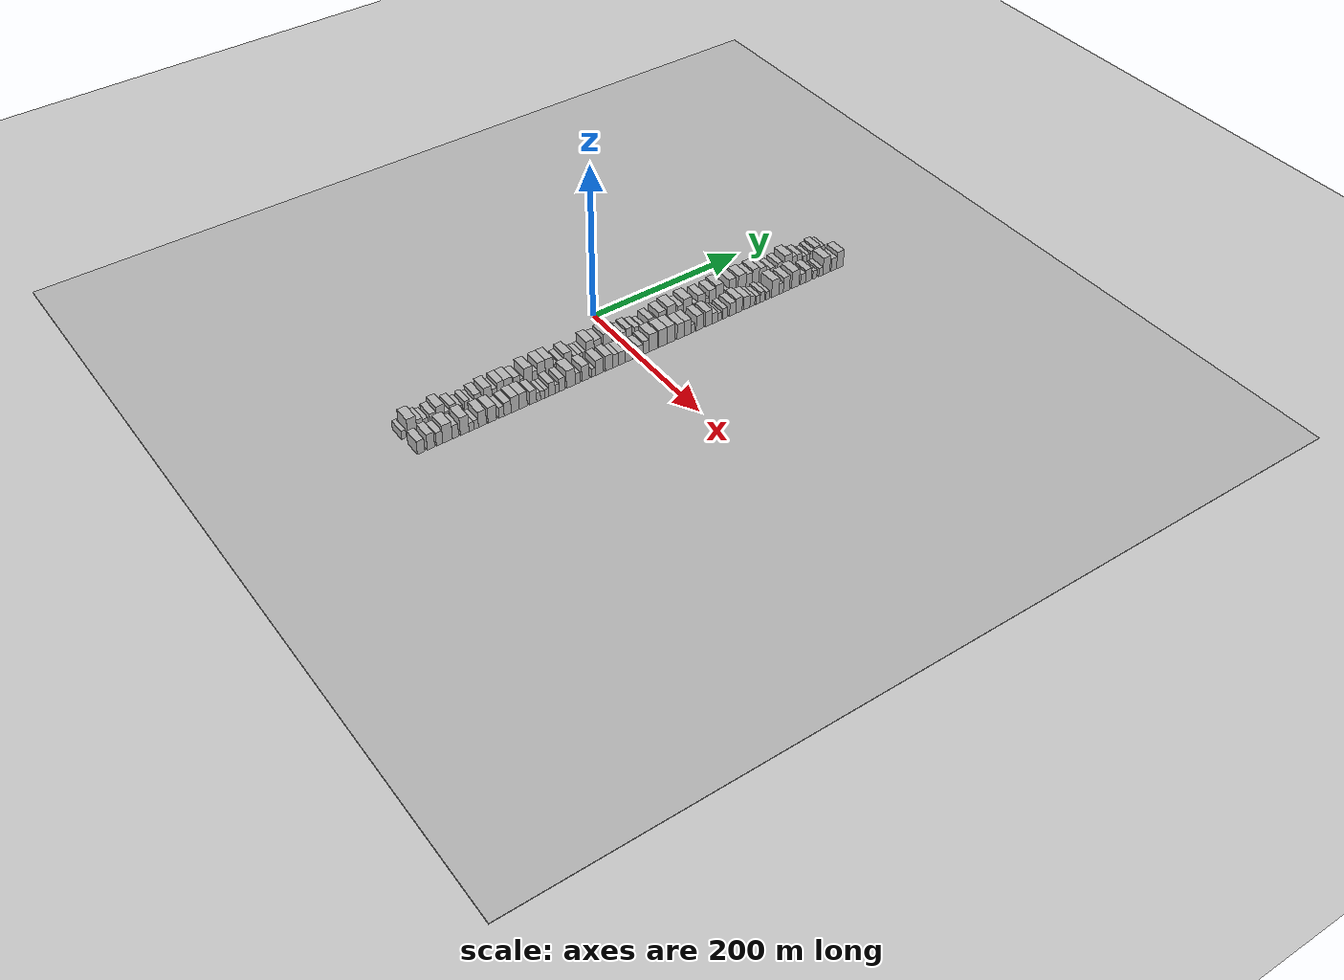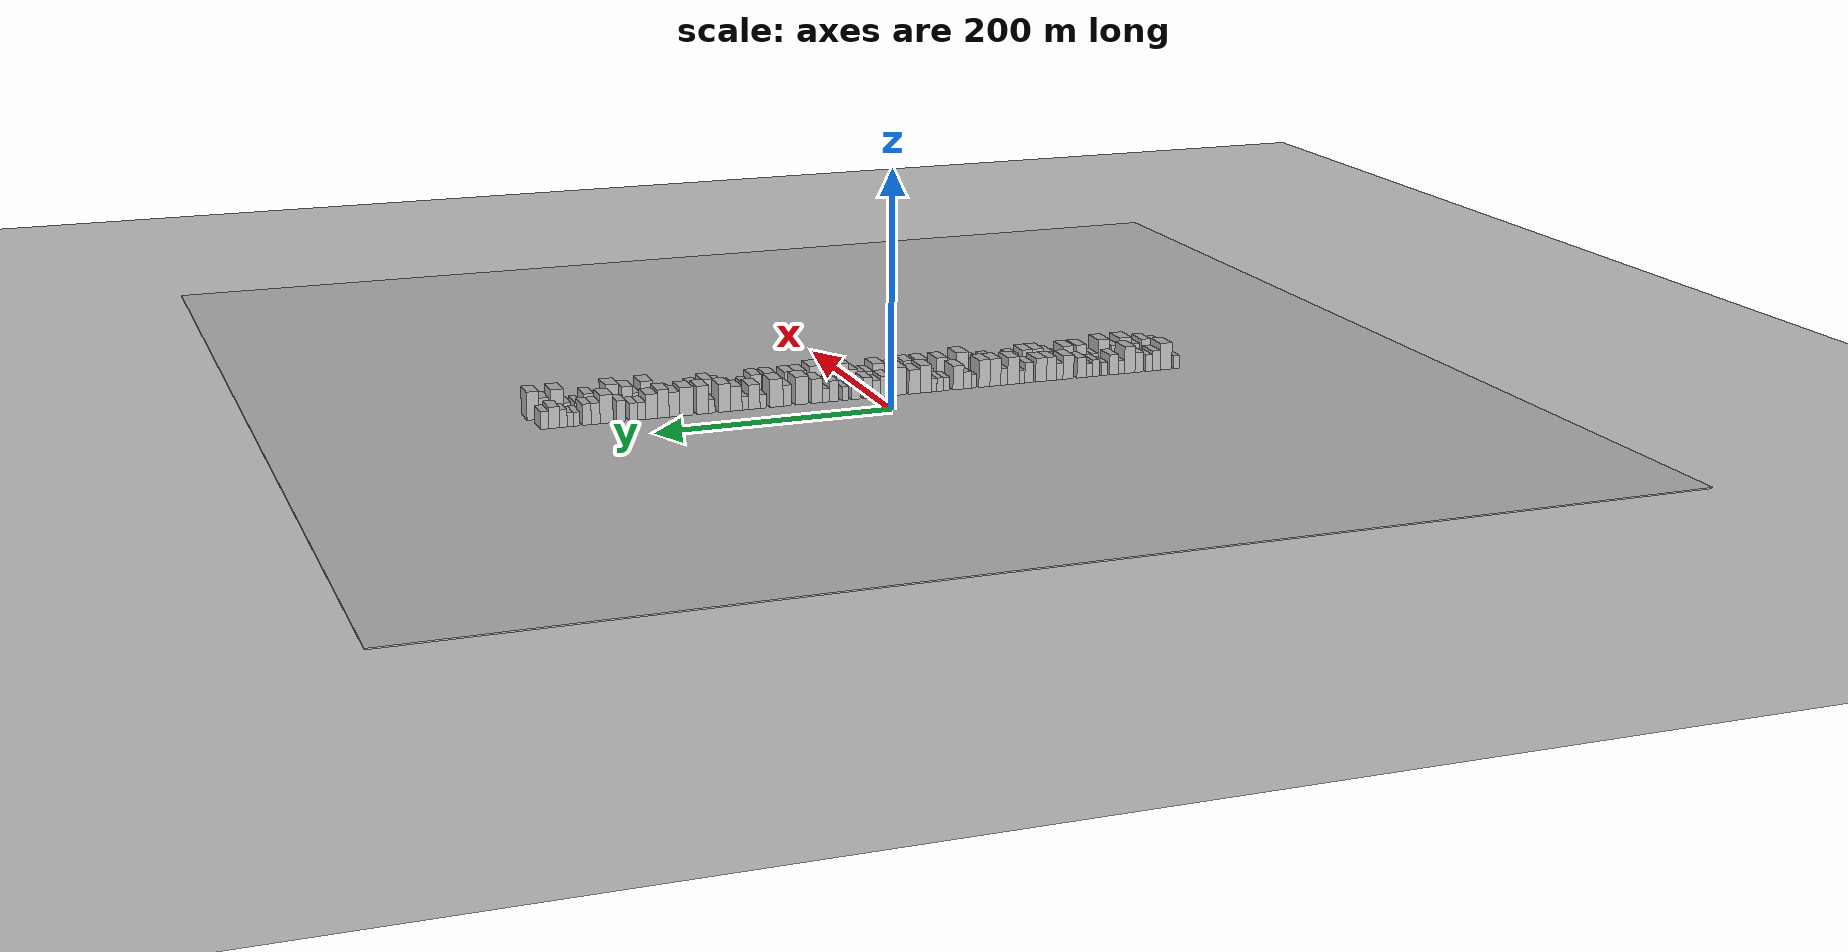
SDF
<?xml version="1.0" encoding="utf-8"?>

<sdf version="1.6">

   <world name="default">

      <gui fullscreen="0">

         <camera name="user_camera">

            <pose>-15 0 4.57585 0 0 0</pose>

            <view_controller>orbit</view_controller>

         </camera>

      </gui>

      <scene>

         <sky>

           <clouds>

             <speed>12</speed>

           </clouds>

         </sky>

         <ambient>0.4 0.4 0.4 1</ambient>

         <background>0.7 0.7 0.7 1</background>

         <shadows>1</shadows>

      </scene>

      <gravity>0 0 -9.8066</gravity>

      <magnetic_field>6e-06 2.3e-05 -4.2e-05</magnetic_field>

      <physics default="0" name="default_physics" type="ode">

         <ode>

            <solver>

               <type>quick</type>

               <iters>10</iters>

               <sor>1.0</sor>

               <use_dynamic_moi_rescaling>0</use_dynamic_moi_rescaling>

            </solver>

            <constraints>

               <cfm>0</cfm>

               <erp>0.2</erp>

               <contact_max_correcting_vel>100</contact_max_correcting_vel>

               <contact_surface_layer>0.001</contact_surface_layer>

            </constraints>

         </ode>

         <max_step_size>0.004</max_step_size>

         <real_time_factor>1</real_time_factor>

         <real_time_update_rate>250</real_time_update_rate>

      </physics>

      <light name="sun" type="directional">

         <cast_shadows>1</cast_shadows>

         <pose>0 0 10 0 0 0</pose>

         <diffuse>0.8 0.8 0.8 1</diffuse>

         <specular>0.2 0.2 0.2 1</specular>

         <attenuation>

            <range>1000</range>

            <constant>0.9</constant>

            <linear>0.01</linear>

            <quadratic>0.001</quadratic>

         </attenuation>

         <direction>-0.5 0.1 -0.9</direction>

      </light>

      <include>

         <name>ground_plane_1</name>

         <uri>model://HANNAS_ground_plane</uri>

         <pose>0 0 0  0 0 0</pose>

      </include>

      <include>

         <name>ground_plane_2</name>

         <uri>model://HANNAS_ground_plane</uri>

         <pose>100 0 0  0 0 0</pose>

      </include>

      <model name="building_1">

         <static>1</static>

         <pose frame="">50.0000 -275.3579 0 0.000000 0.000000 0.000000</pose>

         <link name="link">

            <pose frame="">0 0 6.00 0 0 0</pose>

            <collision name="collision">

               <geometry>

                  <box>

                     <size>20.0000 5.2843 12.0000</size>

                  </box>

               </geometry>

               <max_contacts>10</max_contacts>

               <surface>

                  <contact>

                     <ode/>

                  </contact>

                  <bounce/>

                  <friction>

                     <torsional>

                        <ode/>

                     </torsional>

                     <ode/>

                  </friction>

               </surface>

            </collision>

            <visual name="visual">

               <cast_shadows>0</cast_shadows>

               <geometry>

                  <box>

                     <size>20.0000 5.2843 12.0000</size>

                  </box>

               </geometry>

               <material>

                  <script>

                     <uri>model://HANNAS_wall/materials/scripts</uri>

                     <uri>model://HANNAS_wall/materials/textures</uri>

                     <name>vrc/HANNAS_wall</name>

                  </script>

               </material>

            </visual>

            <self_collide>0</self_collide>

            <enable_wind>0</enable_wind>

            <kinematic>0</kinematic>

         </link>

      </model>

      <model name="building_2">

         <static>1</static>

         <pose frame="">50.0000 -265.2781 0 0.000000 0.000000 0.000000</pose>

         <link name="link">

            <pose frame="">0 0 12.00 0 0 0</pose>

            <collision name="collision">

               <geometry>

                  <box>

                     <size>20.0000 10.8752 24.0000</size>

                  </box>

               </geometry>

               <max_contacts>10</max_contacts>

               <surface>

                  <contact>

                     <ode/>

                  </contact>

                  <bounce/>

                  <friction>

                     <torsional>

                        <ode/>

                     </torsional>

                     <ode/>

                  </friction>

               </surface>

            </collision>

            <visual name="visual">

               <cast_shadows>0</cast_shadows>

               <geometry>

                  <box>

                     <size>20.0000 10.8752 24.0000</size>

                  </box>

               </geometry>

               <material>

                  <script>

                     <uri>model://HANNAS_wall/materials/scripts</uri>

                     <uri>model://HANNAS_wall/materials/textures</uri>

                     <name>vrc/HANNAS_wall</name>

                  </script>

               </material>

            </visual>

            <self_collide>0</self_collide>

            <enable_wind>0</enable_wind>

            <kinematic>0</kinematic>

         </link>

      </model>

      <model name="building_3">

         <static>1</static>

         <pose frame="">50.0000 -256.1429 0 0.000000 0.000000 0.000000</pose>

         <link name="link">

            <pose frame="">0 0 9.00 0 0 0</pose>

            <collision name="collision">

               <geometry>

                  <box>

                     <size>20.0000 7.3953 18.0000</size>

                  </box>

               </geometry>

               <max_contacts>10</max_contacts>

               <surface>

                  <contact>

                     <ode/>

                  </contact>

                  <bounce/>

                  <friction>

                     <torsional>

                        <ode/>

                     </torsional>

                     <ode/>

                  </friction>

               </surface>

            </collision>

            <visual name="visual">

               <cast_shadows>0</cast_shadows>

               <geometry>

                  <box>

                     <size>20.0000 7.3953 18.0000</size>

                  </box>

               </geometry>

               <material>

                  <script>

                     <uri>model://HANNAS_wall/materials/scripts</uri>

                     <uri>model://HANNAS_wall/materials/textures</uri>

                     <name>vrc/HANNAS_wall</name>

                  </script>

               </material>

            </visual>

            <self_collide>0</self_collide>

            <enable_wind>0</enable_wind>

            <kinematic>0</kinematic>

         </link>

      </model>

      <model name="building_4">

         <static>1</static>

         <pose frame="">50.0000 -249.2715 0 0.000000 0.000000 0.000000</pose>

         <link name="link">

            <pose frame="">0 0 7.50 0 0 0</pose>

            <collision name="collision">

               <geometry>

                  <box>

                     <size>20.0000 6.3475 15.0000</size>

                  </box>

               </geometry>

               <max_contacts>10</max_contacts>

               <surface>

                  <contact>

                     <ode/>

                  </contact>

                  <bounce/>

                  <friction>

                     <torsional>

                        <ode/>

                     </torsional>

                     <ode/>

                  </friction>

               </surface>

            </collision>

            <visual name="visual">

               <cast_shadows>0</cast_shadows>

               <geometry>

                  <box>

                     <size>20.0000 6.3475 15.0000</size>

                  </box>

               </geometry>

               <material>

                  <script>

                     <uri>model://HANNAS_wall/materials/scripts</uri>

                     <uri>model://HANNAS_wall/materials/textures</uri>

                     <name>vrc/HANNAS_wall</name>

                  </script>

               </material>

            </visual>

            <self_collide>0</self_collide>

            <enable_wind>0</enable_wind>

            <kinematic>0</kinematic>

         </link>

      </model>

      <model name="building_5">

         <static>1</static>

         <pose frame="">50.0000 -240.1305 0 0.000000 0.000000 0.000000</pose>

         <link name="link">

            <pose frame="">0 0 9.00 0 0 0</pose>

            <collision name="collision">

               <geometry>

                  <box>

                     <size>20.0000 7.9344 18.0000</size>

                  </box>

               </geometry>

               <max_contacts>10</max_contacts>

               <surface>

                  <contact>

                     <ode/>

                  </contact>

                  <bounce/>

                  <friction>

                     <torsional>

                        <ode/>

                     </torsional>

                     <ode/>

                  </friction>

               </surface>

            </collision>

            <visual name="visual">

               <cast_shadows>0</cast_shadows>

               <geometry>

                  <box>

                     <size>20.0000 7.9344 18.0000</size>

                  </box>

               </geometry>

               <material>

                  <script>

                     <uri>model://HANNAS_wall/materials/scripts</uri>

                     <uri>model://HANNAS_wall/materials/textures</uri>

                     <name>vrc/HANNAS_wall</name>

                  </script>

               </material>

            </visual>

            <self_collide>0</self_collide>

            <enable_wind>0</enable_wind>

            <kinematic>0</kinematic>

         </link>

      </model>

      <model name="building_6">

         <static>1</static>

         <pose frame="">50.0000 -231.2084 0 0.000000 0.000000 0.000000</pose>

         <link name="link">

            <pose frame="">0 0 12.00 0 0 0</pose>

            <collision name="collision">

               <geometry>

                  <box>

                     <size>20.0000 9.9098 24.0000</size>

                  </box>

               </geometry>

               <max_contacts>10</max_contacts>

               <surface>

                  <contact>

                     <ode/>

                  </contact>

                  <bounce/>

                  <friction>

                     <torsional>

                        <ode/>

                     </torsional>

                     <ode/>

                  </friction>

               </surface>

            </collision>

            <visual name="visual">

               <cast_shadows>0</cast_shadows>

               <geometry>

                  <box>

                     <size>20.0000 9.9098 24.0000</size>

                  </box>

               </geometry>

               <material>

                  <script>

                     <uri>model://HANNAS_wall/materials/scripts</uri>

                     <uri>model://HANNAS_wall/materials/textures</uri>

                     <name>vrc/HANNAS_wall</name>

                  </script>

               </material>

            </visual>

            <self_collide>0</self_collide>

            <enable_wind>0</enable_wind>

            <kinematic>0</kinematic>

         </link>

      </model>

      <model name="building_7">

         <static>1</static>

         <pose frame="">50.0000 -223.3316 0 0.000000 0.000000 0.000000</pose>

         <link name="link">

            <pose frame="">0 0 6.00 0 0 0</pose>

            <collision name="collision">

               <geometry>

                  <box>

                     <size>20.0000 5.8438 12.0000</size>

                  </box>

               </geometry>

               <max_contacts>10</max_contacts>

               <surface>

                  <contact>

                     <ode/>

                  </contact>

                  <bounce/>

                  <friction>

                     <torsional>

                        <ode/>

                     </torsional>

                     <ode/>

                  </friction>

               </surface>

            </collision>

            <visual name="visual">

               <cast_shadows>0</cast_shadows>

               <geometry>

                  <box>

                     <size>20.0000 5.8438 12.0000</size>

                  </box>

               </geometry>

               <material>

                  <script>

                     <uri>model://HANNAS_wall/materials/scripts</uri>

                     <uri>model://HANNAS_wall/materials/textures</uri>

                     <name>vrc/HANNAS_wall</name>

                  </script>

               </material>

            </visual>

            <self_collide>0</self_collide>

            <enable_wind>0</enable_wind>

            <kinematic>0</kinematic>

         </link>

      </model>

      <model name="building_8">

         <static>1</static>

         <pose frame="">50.0000 -216.3932 0 0.000000 0.000000 0.000000</pose>

         <link name="link">

            <pose frame="">0 0 9.00 0 0 0</pose>

            <collision name="collision">

               <geometry>

                  <box>

                     <size>20.0000 8.0331 18.0000</size>

                  </box>

               </geometry>

               <max_contacts>10</max_contacts>

               <surface>

                  <contact>

                     <ode/>

                  </contact>

                  <bounce/>

                  <friction>

                     <torsional>

                        <ode/>

                     </torsional>

                     <ode/>

                  </friction>

               </surface>

            </collision>

            <visual name="visual">

               <cast_shadows>0</cast_shadows>

               <geometry>

                  <box>

                     <size>20.0000 8.0331 18.0000</size>

                  </box>

               </geometry>

               <material>

                  <script>

                     <uri>model://HANNAS_wall/materials/scripts</uri>

                     <uri>model://HANNAS_wall/materials/textures</uri>

                     <name>vrc/HANNAS_wall</name>

                  </script>

               </material>

            </visual>

            <self_collide>0</self_collide>

            <enable_wind>0</enable_wind>

            <kinematic>0</kinematic>

         </link>

      </model>

      <model name="building_9">

         <static>1</static>

         <pose frame="">50.0000 -207.4719 0 0.000000 0.000000 0.000000</pose>

         <link name="link">

            <pose frame="">0 0 6.00 0 0 0</pose>

            <collision name="collision">

               <geometry>

                  <box>

                     <size>20.0000 5.8093 12.0000</size>

                  </box>

               </geometry>

               <max_contacts>10</max_contacts>

               <surface>

                  <contact>

                     <ode/>

                  </contact>

                  <bounce/>

                  <friction>

                     <torsional>

                        <ode/>

                     </torsional>

                     <ode/>

                  </friction>

               </surface>

            </collision>

            <visual name="visual">

               <cast_shadows>0</cast_shadows>

               <geometry>

                  <box>

                     <size>20.0000 5.8093 12.0000</size>

                  </box>

               </geometry>

               <material>

                  <script>

                     <uri>model://HANNAS_wall/materials/scripts</uri>

                     <uri>model://HANNAS_wall/materials/textures</uri>

                     <name>vrc/HANNAS_wall</name>

                  </script>

               </material>

            </visual>

            <self_collide>0</self_collide>

            <enable_wind>0</enable_wind>

            <kinematic>0</kinematic>

         </link>

      </model>

      <model name="building_10">

         <static>1</static>

         <pose frame="">50.0000 -199.4390 0 0.000000 0.000000 0.000000</pose>

         <link name="link">

            <pose frame="">0 0 7.50 0 0 0</pose>

            <collision name="collision">

               <geometry>

                  <box>

                     <size>20.0000 6.2564 15.0000</size>

                  </box>

               </geometry>

               <max_contacts>10</max_contacts>

               <surface>

                  <contact>

                     <ode/>

                  </contact>

                  <bounce/>

                  <friction>

                     <torsional>

                        <ode/>

                     </torsional>

                     <ode/>

                  </friction>

               </surface>

            </collision>

            <visual name="visual">

               <cast_shadows>0</cast_shadows>

               <geometry>

                  <box>

                     <size>20.0000 6.2564 15.0000</size>

                  </box>

               </geometry>

               <material>

                  <script>

                     <uri>model://HANNAS_wall/materials/scripts</uri>

                     <uri>model://HANNAS_wall/materials/textures</uri>

                     <name>vrc/HANNAS_wall</name>

                  </script>

               </material>

            </visual>

            <self_collide>0</self_collide>

            <enable_wind>0</enable_wind>

            <kinematic>0</kinematic>

         </link>

      </model>

      <model name="building_11">

         <static>1</static>

         <pose frame="">50.0000 -193.6024 0 0.000000 0.000000 0.000000</pose>

         <link name="link">

            <pose frame="">0 0 6.00 0 0 0</pose>

            <collision name="collision">

               <geometry>

                  <box>

                     <size>20.0000 5.4169 12.0000</size>

                  </box>

               </geometry>

               <max_contacts>10</max_contacts>

               <surface>

                  <contact>

                     <ode/>

                  </contact>

                  <bounce/>

                  <friction>

                     <torsional>

                        <ode/>

                     </torsional>

                     <ode/>

                  </friction>

               </surface>

            </collision>

            <visual name="visual">

               <cast_shadows>0</cast_shadows>

               <geometry>

                  <box>

                     <size>20.0000 5.4169 12.0000</size>

                  </box>

               </geometry>

               <material>

                  <script>

                     <uri>model://HANNAS_wall/materials/scripts</uri>

                     <uri>model://HANNAS_wall/materials/textures</uri>

                     <name>vrc/HANNAS_wall</name>

                  </script>

               </material>

            </visual>

            <self_collide>0</self_collide>

            <enable_wind>0</enable_wind>

            <kinematic>0</kinematic>

         </link>

      </model>

      <model name="building_12">

         <static>1</static>

         <pose frame="">50.0000 -186.4434 0 0.000000 0.000000 0.000000</pose>

         <link name="link">

            <pose frame="">0 0 9.00 0 0 0</pose>

            <collision name="collision">

               <geometry>

                  <box>

                     <size>20.0000 8.9011 18.0000</size>

                  </box>

               </geometry>

               <max_contacts>10</max_contacts>

               <surface>

                  <contact>

                     <ode/>

                  </contact>

                  <bounce/>

                  <friction>

                     <torsional>

                        <ode/>

                     </torsional>

                     <ode/>

                  </friction>

               </surface>

            </collision>

            <visual name="visual">

               <cast_shadows>0</cast_shadows>

               <geometry>

                  <box>

                     <size>20.0000 8.9011 18.0000</size>

                  </box>

               </geometry>

               <material>

                  <script>

                     <uri>model://HANNAS_wall/materials/scripts</uri>

                     <uri>model://HANNAS_wall/materials/textures</uri>

                     <name>vrc/HANNAS_wall</name>

                  </script>

               </material>

            </visual>

            <self_collide>0</self_collide>

            <enable_wind>0</enable_wind>

            <kinematic>0</kinematic>

         </link>

      </model>

      <model name="building_13">

         <static>1</static>

         <pose frame="">50.0000 -174.0192 0 0.000000 0.000000 0.000000</pose>

         <link name="link">

            <pose frame="">0 0 10.50 0 0 0</pose>

            <collision name="collision">

               <geometry>

                  <box>

                     <size>20.0000 9.9473 21.0000</size>

                  </box>

               </geometry>

               <max_contacts>10</max_contacts>

               <surface>

                  <contact>

                     <ode/>

                  </contact>

                  <bounce/>

                  <friction>

                     <torsional>

                        <ode/>

                     </torsional>

                     <ode/>

                  </friction>

               </surface>

            </collision>

            <visual name="visual">

               <cast_shadows>0</cast_shadows>

               <geometry>

                  <box>

                     <size>20.0000 9.9473 21.0000</size>

                  </box>

               </geometry>

               <material>

                  <script>

                     <uri>model://HANNAS_wall/materials/scripts</uri>

                     <uri>model://HANNAS_wall/materials/textures</uri>

                     <name>vrc/HANNAS_wall</name>

                  </script>

               </material>

            </visual>

            <self_collide>0</self_collide>

            <enable_wind>0</enable_wind>

            <kinematic>0</kinematic>

         </link>

      </model>

      <model name="building_14">

         <static>1</static>

         <pose frame="">50.0000 -165.8925 0 0.000000 0.000000 0.000000</pose>

         <link name="link">

            <pose frame="">0 0 7.50 0 0 0</pose>

            <collision name="collision">

               <geometry>

                  <box>

                     <size>20.0000 6.3062 15.0000</size>

                  </box>

               </geometry>

               <max_contacts>10</max_contacts>

               <surface>

                  <contact>

                     <ode/>

                  </contact>

                  <bounce/>

                  <friction>

                     <torsional>

                        <ode/>

                     </torsional>

                     <ode/>

                  </friction>

               </surface>

            </collision>

            <visual name="visual">

               <cast_shadows>0</cast_shadows>

               <geometry>

                  <box>

                     <size>20.0000 6.3062 15.0000</size>

                  </box>

               </geometry>

               <material>

                  <script>

                     <uri>model://HANNAS_wall/materials/scripts</uri>

                     <uri>model://HANNAS_wall/materials/textures</uri>

                     <name>vrc/HANNAS_wall</name>

                  </script>

               </material>

            </visual>

            <self_collide>0</self_collide>

            <enable_wind>0</enable_wind>

            <kinematic>0</kinematic>

         </link>

      </model>

      <model name="building_15">

         <static>1</static>

         <pose frame="">50.0000 -158.4266 0 0.000000 0.000000 0.000000</pose>

         <link name="link">

            <pose frame="">0 0 10.50 0 0 0</pose>

            <collision name="collision">

               <geometry>

                  <box>

                     <size>20.0000 8.6257 21.0000</size>

                  </box>

               </geometry>

               <max_contacts>10</max_contacts>

               <surface>

                  <contact>

                     <ode/>

                  </contact>

                  <bounce/>

                  <friction>

                     <torsional>

                        <ode/>

                     </torsional>

                     <ode/>

                  </friction>

               </surface>

            </collision>

            <visual name="visual">

               <cast_shadows>0</cast_shadows>

               <geometry>

                  <box>

                     <size>20.0000 8.6257 21.0000</size>

                  </box>

               </geometry>

               <material>

                  <script>

                     <uri>model://HANNAS_wall/materials/scripts</uri>

                     <uri>model://HANNAS_wall/materials/textures</uri>

                     <name>vrc/HANNAS_wall</name>

                  </script>

               </material>

            </visual>

            <self_collide>0</self_collide>

            <enable_wind>0</enable_wind>

            <kinematic>0</kinematic>

         </link>

      </model>

      <model name="building_16">

         <static>1</static>

         <pose frame="">50.0000 -149.0510 0 0.000000 0.000000 0.000000</pose>

         <link name="link">

            <pose frame="">0 0 10.50 0 0 0</pose>

            <collision name="collision">

               <geometry>

                  <box>

                     <size>20.0000 10.1255 21.0000</size>

                  </box>

               </geometry>

               <max_contacts>10</max_contacts>

               <surface>

                  <contact>

                     <ode/>

                  </contact>

                  <bounce/>

                  <friction>

                     <torsional>

                        <ode/>

                     </torsional>

                     <ode/>

                  </friction>

               </surface>

            </collision>

            <visual name="visual">

               <cast_shadows>0</cast_shadows>

               <geometry>

                  <box>

                     <size>20.0000 10.1255 21.0000</size>

                  </box>

               </geometry>

               <material>

                  <script>

                     <uri>model://HANNAS_wall/materials/scripts</uri>

                     <uri>model://HANNAS_wall/materials/textures</uri>

                     <name>vrc/HANNAS_wall</name>

                  </script>

               </material>

            </visual>

            <self_collide>0</self_collide>

            <enable_wind>0</enable_wind>

            <kinematic>0</kinematic>

         </link>

      </model>

      <model name="building_17">

         <static>1</static>

         <pose frame="">50.0000 -138.0163 0 0.000000 0.000000 0.000000</pose>

         <link name="link">

            <pose frame="">0 0 9.00 0 0 0</pose>

            <collision name="collision">

               <geometry>

                  <box>

                     <size>20.0000 7.9438 18.0000</size>

                  </box>

               </geometry>

               <max_contacts>10</max_contacts>

               <surface>

                  <contact>

                     <ode/>

                  </contact>

                  <bounce/>

                  <friction>

                     <torsional>

                        <ode/>

                     </torsional>

                     <ode/>

                  </friction>

               </surface>

            </collision>

            <visual name="visual">

               <cast_shadows>0</cast_shadows>

               <geometry>

                  <box>

                     <size>20.0000 7.9438 18.0000</size>

                  </box>

               </geometry>

               <material>

                  <script>

                     <uri>model://HANNAS_wall/materials/scripts</uri>

                     <uri>model://HANNAS_wall/materials/textures</uri>

                     <name>vrc/HANNAS_wall</name>

                  </script>

               </material>

            </visual>

            <self_collide>0</self_collide>

            <enable_wind>0</enable_wind>

            <kinematic>0</kinematic>

         </link>

      </model>

      <model name="building_18">

         <static>1</static>

         <pose frame="">50.0000 -131.5316 0 0.000000 0.000000 0.000000</pose>

         <link name="link">

            <pose frame="">0 0 6.00 0 0 0</pose>

            <collision name="collision">

               <geometry>

                  <box>

                     <size>20.0000 5.0256 12.0000</size>

                  </box>

               </geometry>

               <max_contacts>10</max_contacts>

               <surface>

                  <contact>

                     <ode/>

                  </contact>

                  <bounce/>

                  <friction>

                     <torsional>

                        <ode/>

                     </torsional>

                     <ode/>

                  </friction>

               </surface>

            </collision>

            <visual name="visual">

               <cast_shadows>0</cast_shadows>

               <geometry>

                  <box>

                     <size>20.0000 5.0256 12.0000</size>

                  </box>

               </geometry>

               <material>

                  <script>

                     <uri>model://HANNAS_wall/materials/scripts</uri>

                     <uri>model://HANNAS_wall/materials/textures</uri>

                     <name>vrc/HANNAS_wall</name>

                  </script>

               </material>

            </visual>

            <self_collide>0</self_collide>

            <enable_wind>0</enable_wind>

            <kinematic>0</kinematic>

         </link>

      </model>

      <model name="building_19">

         <static>1</static>

         <pose frame="">50.0000 -123.7338 0 0.000000 0.000000 0.000000</pose>

         <link name="link">

            <pose frame="">0 0 12.00 0 0 0</pose>

            <collision name="collision">

               <geometry>

                  <box>

                     <size>20.0000 10.5699 24.0000</size>

                  </box>

               </geometry>

               <max_contacts>10</max_contacts>

               <surface>

                  <contact>

                     <ode/>

                  </contact>

                  <bounce/>

                  <friction>

                     <torsional>

                        <ode/>

                     </torsional>

                     <ode/>

                  </friction>

               </surface>

            </collision>

            <visual name="visual">

               <cast_shadows>0</cast_shadows>

               <geometry>

                  <box>

                     <size>20.0000 10.5699 24.0000</size>

                  </box>

               </geometry>

               <material>

                  <script>

                     <uri>model://HANNAS_wall/materials/scripts</uri>

                     <uri>model://HANNAS_wall/materials/textures</uri>

                     <name>vrc/HANNAS_wall</name>

                  </script>

               </material>

            </visual>

            <self_collide>0</self_collide>

            <enable_wind>0</enable_wind>

            <kinematic>0</kinematic>

         </link>

      </model>

      <model name="building_20">

         <static>1</static>

         <pose frame="">50.0000 -115.3084 0 0.000000 0.000000 0.000000</pose>

         <link name="link">

            <pose frame="">0 0 7.50 0 0 0</pose>

            <collision name="collision">

               <geometry>

                  <box>

                     <size>20.0000 6.2810 15.0000</size>

                  </box>

               </geometry>

               <max_contacts>10</max_contacts>

               <surface>

                  <contact>

                     <ode/>

                  </contact>

                  <bounce/>

                  <friction>

                     <torsional>

                        <ode/>

                     </torsional>

                     <ode/>

                  </friction>

               </surface>

            </collision>

            <visual name="visual">

               <cast_shadows>0</cast_shadows>

               <geometry>

                  <box>

                     <size>20.0000 6.2810 15.0000</size>

                  </box>

               </geometry>

               <material>

                  <script>

                     <uri>model://HANNAS_wall/materials/scripts</uri>

                     <uri>model://HANNAS_wall/materials/textures</uri>

                     <name>vrc/HANNAS_wall</name>

                  </script>

               </material>

            </visual>

            <self_collide>0</self_collide>

            <enable_wind>0</enable_wind>

            <kinematic>0</kinematic>

         </link>

      </model>

      <model name="building_21">

         <static>1</static>

         <pose frame="">50.0000 -107.2324 0 0.000000 0.000000 0.000000</pose>

         <link name="link">

            <pose frame="">0 0 12.00 0 0 0</pose>

            <collision name="collision">

               <geometry>

                  <box>

                     <size>20.0000 9.8711 24.0000</size>

                  </box>

               </geometry>

               <max_contacts>10</max_contacts>

               <surface>

                  <contact>

                     <ode/>

                  </contact>

                  <bounce/>

                  <friction>

                     <torsional>

                        <ode/>

                     </torsional>

                     <ode/>

                  </friction>

               </surface>

            </collision>

            <visual name="visual">

               <cast_shadows>0</cast_shadows>

               <geometry>

                  <box>

                     <size>20.0000 9.8711 24.0000</size>

                  </box>

               </geometry>

               <material>

                  <script>

                     <uri>model://HANNAS_wall/materials/scripts</uri>

                     <uri>model://HANNAS_wall/materials/textures</uri>

                     <name>vrc/HANNAS_wall</name>

                  </script>

               </material>

            </visual>

            <self_collide>0</self_collide>

            <enable_wind>0</enable_wind>

            <kinematic>0</kinematic>

         </link>

      </model>

      <model name="building_22">

         <static>1</static>

         <pose frame="">50.0000 -97.2972 0 0.000000 0.000000 0.000000</pose>

         <link name="link">

            <pose frame="">0 0 12.00 0 0 0</pose>

            <collision name="collision">

               <geometry>

                  <box>

                     <size>20.0000 9.9993 24.0000</size>

                  </box>

               </geometry>

               <max_contacts>10</max_contacts>

               <surface>

                  <contact>

                     <ode/>

                  </contact>

                  <bounce/>

                  <friction>

                     <torsional>

                        <ode/>

                     </torsional>

                     <ode/>

                  </friction>

               </surface>

            </collision>

            <visual name="visual">

               <cast_shadows>0</cast_shadows>

               <geometry>

                  <box>

                     <size>20.0000 9.9993 24.0000</size>

                  </box>

               </geometry>

               <material>

                  <script>

                     <uri>model://HANNAS_wall/materials/scripts</uri>

                     <uri>model://HANNAS_wall/materials/textures</uri>

                     <name>vrc/HANNAS_wall</name>

                  </script>

               </material>

            </visual>

            <self_collide>0</self_collide>

            <enable_wind>0</enable_wind>

            <kinematic>0</kinematic>

         </link>

      </model>

      <model name="building_23">

         <static>1</static>

         <pose frame="">50.0000 -87.7939 0 0.000000 0.000000 0.000000</pose>

         <link name="link">

            <pose frame="">0 0 6.00 0 0 0</pose>

            <collision name="collision">

               <geometry>

                  <box>

                     <size>20.0000 5.0073 12.0000</size>

                  </box>

               </geometry>

               <max_contacts>10</max_contacts>

               <surface>

                  <contact>

                     <ode/>

                  </contact>

                  <bounce/>

                  <friction>

                     <torsional>

                        <ode/>

                     </torsional>

                     <ode/>

                  </friction>

               </surface>

            </collision>

            <visual name="visual">

               <cast_shadows>0</cast_shadows>

               <geometry>

                  <box>

                     <size>20.0000 5.0073 12.0000</size>

                  </box>

               </geometry>

               <material>

                  <script>

                     <uri>model://HANNAS_wall/materials/scripts</uri>

                     <uri>model://HANNAS_wall/materials/textures</uri>

                     <name>vrc/HANNAS_wall</name>

                  </script>

               </material>

            </visual>

            <self_collide>0</self_collide>

            <enable_wind>0</enable_wind>

            <kinematic>0</kinematic>

         </link>

      </model>

      <model name="building_24">

         <static>1</static>

         <pose frame="">50.0000 -81.9762 0 0.000000 0.000000 0.000000</pose>

         <link name="link">

            <pose frame="">0 0 7.50 0 0 0</pose>

            <collision name="collision">

               <geometry>

                  <box>

                     <size>20.0000 6.6281 15.0000</size>

                  </box>

               </geometry>

               <max_contacts>10</max_contacts>

               <surface>

                  <contact>

                     <ode/>

                  </contact>

                  <bounce/>

                  <friction>

                     <torsional>

                        <ode/>

                     </torsional>

                     <ode/>

                  </friction>

               </surface>

            </collision>

            <visual name="visual">

               <cast_shadows>0</cast_shadows>

               <geometry>

                  <box>

                     <size>20.0000 6.6281 15.0000</size>

                  </box>

               </geometry>

               <material>

                  <script>

                     <uri>model://HANNAS_wall/materials/scripts</uri>

                     <uri>model://HANNAS_wall/materials/textures</uri>

                     <name>vrc/HANNAS_wall</name>

                  </script>

               </material>

            </visual>

            <self_collide>0</self_collide>

            <enable_wind>0</enable_wind>

            <kinematic>0</kinematic>

         </link>

      </model>

      <model name="building_25">

         <static>1</static>

         <pose frame="">50.0000 -73.7933 0 0.000000 0.000000 0.000000</pose>

         <link name="link">

            <pose frame="">0 0 10.50 0 0 0</pose>

            <collision name="collision">

               <geometry>

                  <box>

                     <size>20.0000 9.7376 21.0000</size>

                  </box>

               </geometry>

               <max_contacts>10</max_contacts>

               <surface>

                  <contact>

                     <ode/>

                  </contact>

                  <bounce/>

                  <friction>

                     <torsional>

                        <ode/>

                     </torsional>

                     <ode/>

                  </friction>

               </surface>

            </collision>

            <visual name="visual">

               <cast_shadows>0</cast_shadows>

               <geometry>

                  <box>

                     <size>20.0000 9.7376 21.0000</size>

                  </box>

               </geometry>

               <material>

                  <script>

                     <uri>model://HANNAS_wall/materials/scripts</uri>

                     <uri>model://HANNAS_wall/materials/textures</uri>

                     <name>vrc/HANNAS_wall</name>

                  </script>

               </material>

            </visual>

            <self_collide>0</self_collide>

            <enable_wind>0</enable_wind>

            <kinematic>0</kinematic>

         </link>

      </model>

      <model name="building_26">

         <static>1</static>

         <pose frame="">50.0000 -63.0612 0 0.000000 0.000000 0.000000</pose>

         <link name="link">

            <pose frame="">0 0 6.00 0 0 0</pose>

            <collision name="collision">

               <geometry>

                  <box>

                     <size>20.0000 5.7266 12.0000</size>

                  </box>

               </geometry>

               <max_contacts>10</max_contacts>

               <surface>

                  <contact>

                     <ode/>

                  </contact>

                  <bounce/>

                  <friction>

                     <torsional>

                        <ode/>

                     </torsional>

                     <ode/>

                  </friction>

               </surface>

            </collision>

            <visual name="visual">

               <cast_shadows>0</cast_shadows>

               <geometry>

                  <box>

                     <size>20.0000 5.7266 12.0000</size>

                  </box>

               </geometry>

               <material>

                  <script>

                     <uri>model://HANNAS_wall/materials/scripts</uri>

                     <uri>model://HANNAS_wall/materials/textures</uri>

                     <name>vrc/HANNAS_wall</name>

                  </script>

               </material>

            </visual>

            <self_collide>0</self_collide>

            <enable_wind>0</enable_wind>

            <kinematic>0</kinematic>

         </link>

      </model>

      <model name="building_27">

         <static>1</static>

         <pose frame="">50.0000 -57.3837 0 0.000000 0.000000 0.000000</pose>

         <link name="link">

            <pose frame="">0 0 6.00 0 0 0</pose>

            <collision name="collision">

               <geometry>

                  <box>

                     <size>20.0000 5.6284 12.0000</size>

                  </box>

               </geometry>

               <max_contacts>10</max_contacts>

               <surface>

                  <contact>

                     <ode/>

                  </contact>

                  <bounce/>

                  <friction>

                     <torsional>

                        <ode/>

                     </torsional>

                     <ode/>

                  </friction>

               </surface>

            </collision>

            <visual name="visual">

               <cast_shadows>0</cast_shadows>

               <geometry>

                  <box>

                     <size>20.0000 5.6284 12.0000</size>

                  </box>

               </geometry>

               <material>

                  <script>

                     <uri>model://HANNAS_wall/materials/scripts</uri>

                     <uri>model://HANNAS_wall/materials/textures</uri>

                     <name>vrc/HANNAS_wall</name>

                  </script>

               </material>

            </visual>

            <self_collide>0</self_collide>

            <enable_wind>0</enable_wind>

            <kinematic>0</kinematic>

         </link>

      </model>

      <model name="building_28">

         <static>1</static>

         <pose frame="">50.0000 -52.1638 0 0.000000 0.000000 0.000000</pose>

         <link name="link">

            <pose frame="">0 0 6.00 0 0 0</pose>

            <collision name="collision">

               <geometry>

                  <box>

                     <size>20.0000 4.8116 12.0000</size>

                  </box>

               </geometry>

               <max_contacts>10</max_contacts>

               <surface>

                  <contact>

                     <ode/>

                  </contact>

                  <bounce/>

                  <friction>

                     <torsional>

                        <ode/>

                     </torsional>

                     <ode/>

                  </friction>

               </surface>

            </collision>

            <visual name="visual">

               <cast_shadows>0</cast_shadows>

               <geometry>

                  <box>

                     <size>20.0000 4.8116 12.0000</size>

                  </box>

               </geometry>

               <material>

                  <script>

                     <uri>model://HANNAS_wall/materials/scripts</uri>

                     <uri>model://HANNAS_wall/materials/textures</uri>

                     <name>vrc/HANNAS_wall</name>

                  </script>

               </material>

            </visual>

            <self_collide>0</self_collide>

            <enable_wind>0</enable_wind>

            <kinematic>0</kinematic>

         </link>

      </model>

      <model name="building_29">

         <static>1</static>

         <pose frame="">50.0000 -44.6425 0 0.000000 0.000000 0.000000</pose>

         <link name="link">

            <pose frame="">0 0 12.00 0 0 0</pose>

            <collision name="collision">

               <geometry>

                  <box>

                     <size>20.0000 10.2310 24.0000</size>

                  </box>

               </geometry>

               <max_contacts>10</max_contacts>

               <surface>

                  <contact>

                     <ode/>

                  </contact>

                  <bounce/>

                  <friction>

                     <torsional>

                        <ode/>

                     </torsional>

                     <ode/>

                  </friction>

               </surface>

            </collision>

            <visual name="visual">

               <cast_shadows>0</cast_shadows>

               <geometry>

                  <box>

                     <size>20.0000 10.2310 24.0000</size>

                  </box>

               </geometry>

               <material>

                  <script>

                     <uri>model://HANNAS_wall/materials/scripts</uri>

                     <uri>model://HANNAS_wall/materials/textures</uri>

                     <name>vrc/HANNAS_wall</name>

                  </script>

               </material>

            </visual>

            <self_collide>0</self_collide>

            <enable_wind>0</enable_wind>

            <kinematic>0</kinematic>

         </link>

      </model>

      <model name="building_30">

         <static>1</static>

         <pose frame="">50.0000 -34.5678 0 0.000000 0.000000 0.000000</pose>

         <link name="link">

            <pose frame="">0 0 10.50 0 0 0</pose>

            <collision name="collision">

               <geometry>

                  <box>

                     <size>20.0000 9.9183 21.0000</size>

                  </box>

               </geometry>

               <max_contacts>10</max_contacts>

               <surface>

                  <contact>

                     <ode/>

                  </contact>

                  <bounce/>

                  <friction>

                     <torsional>

                        <ode/>

                     </torsional>

                     <ode/>

                  </friction>

               </surface>

            </collision>

            <visual name="visual">

               <cast_shadows>0</cast_shadows>

               <geometry>

                  <box>

                     <size>20.0000 9.9183 21.0000</size>

                  </box>

               </geometry>

               <material>

                  <script>

                     <uri>model://HANNAS_wall/materials/scripts</uri>

                     <uri>model://HANNAS_wall/materials/textures</uri>

                     <name>vrc/HANNAS_wall</name>

                  </script>

               </material>

            </visual>

            <self_collide>0</self_collide>

            <enable_wind>0</enable_wind>

            <kinematic>0</kinematic>

         </link>

      </model>

      <model name="building_31">

         <static>1</static>

         <pose frame="">50.0000 -21.7144 0 0.000000 0.000000 0.000000</pose>

         <link name="link">

            <pose frame="">0 0 12.00 0 0 0</pose>

            <collision name="collision">

               <geometry>

                  <box>

                     <size>20.0000 11.7885 24.0000</size>

                  </box>

               </geometry>

               <max_contacts>10</max_contacts>

               <surface>

                  <contact>

                     <ode/>

                  </contact>

                  <bounce/>

                  <friction>

                     <torsional>

                        <ode/>

                     </torsional>

                     <ode/>

                  </friction>

               </surface>

            </collision>

            <visual name="visual">

               <cast_shadows>0</cast_shadows>

               <geometry>

                  <box>

                     <size>20.0000 11.7885 24.0000</size>

                  </box>

               </geometry>

               <material>

                  <script>

                     <uri>model://HANNAS_wall/materials/scripts</uri>

                     <uri>model://HANNAS_wall/materials/textures</uri>

                     <name>vrc/HANNAS_wall</name>

                  </script>

               </material>

            </visual>

            <self_collide>0</self_collide>

            <enable_wind>0</enable_wind>

            <kinematic>0</kinematic>

         </link>

      </model>

      <model name="building_32">

         <static>1</static>

         <pose frame="">50.0000 -8.7360 0 0.000000 0.000000 0.000000</pose>

         <link name="link">

            <pose frame="">0 0 9.00 0 0 0</pose>

            <collision name="collision">

               <geometry>

                  <box>

                     <size>20.0000 8.1682 18.0000</size>

                  </box>

               </geometry>

               <max_contacts>10</max_contacts>

               <surface>

                  <contact>

                     <ode/>

                  </contact>

                  <bounce/>

                  <friction>

                     <torsional>

                        <ode/>

                     </torsional>

                     <ode/>

                  </friction>

               </surface>

            </collision>

            <visual name="visual">

               <cast_shadows>0</cast_shadows>

               <geometry>

                  <box>

                     <size>20.0000 8.1682 18.0000</size>

                  </box>

               </geometry>

               <material>

                  <script>

                     <uri>model://HANNAS_wall/materials/scripts</uri>

                     <uri>model://HANNAS_wall/materials/textures</uri>

                     <name>vrc/HANNAS_wall</name>

                  </script>

               </material>

            </visual>

            <self_collide>0</self_collide>

            <enable_wind>0</enable_wind>

            <kinematic>0</kinematic>

         </link>

      </model>

      <model name="building_33">

         <static>1</static>

         <pose frame="">50.0000 -0.9373 0 0.000000 0.000000 0.000000</pose>

         <link name="link">

            <pose frame="">0 0 7.50 0 0 0</pose>

            <collision name="collision">

               <geometry>

                  <box>

                     <size>20.0000 7.4293 15.0000</size>

                  </box>

               </geometry>

               <max_contacts>10</max_contacts>

               <surface>

                  <contact>

                     <ode/>

                  </contact>

                  <bounce/>

                  <friction>

                     <torsional>

                        <ode/>

                     </torsional>

                     <ode/>

                  </friction>

               </surface>

            </collision>

            <visual name="visual">

               <cast_shadows>0</cast_shadows>

               <geometry>

                  <box>

                     <size>20.0000 7.4293 15.0000</size>

                  </box>

               </geometry>

               <material>

                  <script>

                     <uri>model://HANNAS_wall/materials/scripts</uri>

                     <uri>model://HANNAS_wall/materials/textures</uri>

                     <name>vrc/HANNAS_wall</name>

                  </script>

               </material>

            </visual>

            <self_collide>0</self_collide>

            <enable_wind>0</enable_wind>

            <kinematic>0</kinematic>

         </link>

      </model>

      <model name="building_34">

         <static>1</static>

         <pose frame="">50.0000 6.6551 0 0.000000 0.000000 0.000000</pose>

         <link name="link">

            <pose frame="">0 0 9.00 0 0 0</pose>

            <collision name="collision">

               <geometry>

                  <box>

                     <size>20.0000 7.7553 18.0000</size>

                  </box>

               </geometry>

               <max_contacts>10</max_contacts>

               <surface>

                  <contact>

                     <ode/>

                  </contact>

                  <bounce/>

                  <friction>

                     <torsional>

                        <ode/>

                     </torsional>

                     <ode/>

                  </friction>

               </surface>

            </collision>

            <visual name="visual">

               <cast_shadows>0</cast_shadows>

               <geometry>

                  <box>

                     <size>20.0000 7.7553 18.0000</size>

                  </box>

               </geometry>

               <material>

                  <script>

                     <uri>model://HANNAS_wall/materials/scripts</uri>

                     <uri>model://HANNAS_wall/materials/textures</uri>

                     <name>vrc/HANNAS_wall</name>

                  </script>

               </material>

            </visual>

            <self_collide>0</self_collide>

            <enable_wind>0</enable_wind>

            <kinematic>0</kinematic>

         </link>

      </model>

      <model name="building_35">

         <static>1</static>

         <pose frame="">50.0000 17.1252 0 0.000000 0.000000 0.000000</pose>

         <link name="link">

            <pose frame="">0 0 7.50 0 0 0</pose>

            <collision name="collision">

               <geometry>

                  <box>

                     <size>20.0000 7.1849 15.0000</size>

                  </box>

               </geometry>

               <max_contacts>10</max_contacts>

               <surface>

                  <contact>

                     <ode/>

                  </contact>

                  <bounce/>

                  <friction>

                     <torsional>

                        <ode/>

                     </torsional>

                     <ode/>

                  </friction>

               </surface>

            </collision>

            <visual name="visual">

               <cast_shadows>0</cast_shadows>

               <geometry>

                  <box>

                     <size>20.0000 7.1849 15.0000</size>

                  </box>

               </geometry>

               <material>

                  <script>

                     <uri>model://HANNAS_wall/materials/scripts</uri>

                     <uri>model://HANNAS_wall/materials/textures</uri>

                     <name>vrc/HANNAS_wall</name>

                  </script>

               </material>

            </visual>

            <self_collide>0</self_collide>

            <enable_wind>0</enable_wind>

            <kinematic>0</kinematic>

         </link>

      </model>

      <model name="building_36">

         <static>1</static>

         <pose frame="">50.0000 26.4992 0 0.000000 0.000000 0.000000</pose>

         <link name="link">

            <pose frame="">0 0 6.00 0 0 0</pose>

            <collision name="collision">

               <geometry>

                  <box>

                     <size>20.0000 5.5631 12.0000</size>

                  </box>

               </geometry>

               <max_contacts>10</max_contacts>

               <surface>

                  <contact>

                     <ode/>

                  </contact>

                  <bounce/>

                  <friction>

                     <torsional>

                        <ode/>

                     </torsional>

                     <ode/>

                  </friction>

               </surface>

            </collision>

            <visual name="visual">

               <cast_shadows>0</cast_shadows>

               <geometry>

                  <box>

                     <size>20.0000 5.5631 12.0000</size>

                  </box>

               </geometry>

               <material>

                  <script>

                     <uri>model://HANNAS_wall/materials/scripts</uri>

                     <uri>model://HANNAS_wall/materials/textures</uri>

                     <name>vrc/HANNAS_wall</name>

                  </script>

               </material>

            </visual>

            <self_collide>0</self_collide>

            <enable_wind>0</enable_wind>

            <kinematic>0</kinematic>

         </link>

      </model>

      <model name="building_37">

         <static>1</static>

         <pose frame="">50.0000 36.3989 0 0.000000 0.000000 0.000000</pose>

         <link name="link">

            <pose frame="">0 0 9.00 0 0 0</pose>

            <collision name="collision">

               <geometry>

                  <box>

                     <size>20.0000 8.2364 18.0000</size>

                  </box>

               </geometry>

               <max_contacts>10</max_contacts>

               <surface>

                  <contact>

                     <ode/>

                  </contact>

                  <bounce/>

                  <friction>

                     <torsional>

                        <ode/>

                     </torsional>

                     <ode/>

                  </friction>

               </surface>

            </collision>

            <visual name="visual">

               <cast_shadows>0</cast_shadows>

               <geometry>

                  <box>

                     <size>20.0000 8.2364 18.0000</size>

                  </box>

               </geometry>

               <material>

                  <script>

                     <uri>model://HANNAS_wall/materials/scripts</uri>

                     <uri>model://HANNAS_wall/materials/textures</uri>

                     <name>vrc/HANNAS_wall</name>

                  </script>

               </material>

            </visual>

            <self_collide>0</self_collide>

            <enable_wind>0</enable_wind>

            <kinematic>0</kinematic>

         </link>

      </model>

      <model name="building_38">

         <static>1</static>

         <pose frame="">50.0000 43.5059 0 0.000000 0.000000 0.000000</pose>

         <link name="link">

            <pose frame="">0 0 6.00 0 0 0</pose>

            <collision name="collision">

               <geometry>

                  <box>

                     <size>20.0000 5.9776 12.0000</size>

                  </box>

               </geometry>

               <max_contacts>10</max_contacts>

               <surface>

                  <contact>

                     <ode/>

                  </contact>

                  <bounce/>

                  <friction>

                     <torsional>

                        <ode/>

                     </torsional>

                     <ode/>

                  </friction>

               </surface>

            </collision>

            <visual name="visual">

               <cast_shadows>0</cast_shadows>

               <geometry>

                  <box>

                     <size>20.0000 5.9776 12.0000</size>

                  </box>

               </geometry>

               <material>

                  <script>

                     <uri>model://HANNAS_wall/materials/scripts</uri>

                     <uri>model://HANNAS_wall/materials/textures</uri>

                     <name>vrc/HANNAS_wall</name>

                  </script>

               </material>

            </visual>

            <self_collide>0</self_collide>

            <enable_wind>0</enable_wind>

            <kinematic>0</kinematic>

         </link>

      </model>

      <model name="building_39">

         <static>1</static>

         <pose frame="">50.0000 51.3330 0 0.000000 0.000000 0.000000</pose>

         <link name="link">

            <pose frame="">0 0 10.50 0 0 0</pose>

            <collision name="collision">

               <geometry>

                  <box>

                     <size>20.0000 9.6765 21.0000</size>

                  </box>

               </geometry>

               <max_contacts>10</max_contacts>

               <surface>

                  <contact>

                     <ode/>

                  </contact>

                  <bounce/>

                  <friction>

                     <torsional>

                        <ode/>

                     </torsional>

                     <ode/>

                  </friction>

               </surface>

            </collision>

            <visual name="visual">

               <cast_shadows>0</cast_shadows>

               <geometry>

                  <box>

                     <size>20.0000 9.6765 21.0000</size>

                  </box>

               </geometry>

               <material>

                  <script>

                     <uri>model://HANNAS_wall/materials/scripts</uri>

                     <uri>model://HANNAS_wall/materials/textures</uri>

                     <name>vrc/HANNAS_wall</name>

                  </script>

               </material>

            </visual>

            <self_collide>0</self_collide>

            <enable_wind>0</enable_wind>

            <kinematic>0</kinematic>

         </link>

      </model>

      <model name="building_40">

         <static>1</static>

         <pose frame="">50.0000 63.9703 0 0.000000 0.000000 0.000000</pose>

         <link name="link">

            <pose frame="">0 0 12.00 0 0 0</pose>

            <collision name="collision">

               <geometry>

                  <box>

                     <size>20.0000 11.5981 24.0000</size>

                  </box>

               </geometry>

               <max_contacts>10</max_contacts>

               <surface>

                  <contact>

                     <ode/>

                  </contact>

                  <bounce/>

                  <friction>

                     <torsional>

                        <ode/>

                     </torsional>

                     <ode/>

                  </friction>

               </surface>

            </collision>

            <visual name="visual">

               <cast_shadows>0</cast_shadows>

               <geometry>

                  <box>

                     <size>20.0000 11.5981 24.0000</size>

                  </box>

               </geometry>

               <material>

                  <script>

                     <uri>model://HANNAS_wall/materials/scripts</uri>

                     <uri>model://HANNAS_wall/materials/textures</uri>

                     <name>vrc/HANNAS_wall</name>

                  </script>

               </material>

            </visual>

            <self_collide>0</self_collide>

            <enable_wind>0</enable_wind>

            <kinematic>0</kinematic>

         </link>

      </model>

      <model name="building_41">

         <static>1</static>

         <pose frame="">50.0000 76.5834 0 0.000000 0.000000 0.000000</pose>

         <link name="link">

            <pose frame="">0 0 9.00 0 0 0</pose>

            <collision name="collision">

               <geometry>

                  <box>

                     <size>20.0000 7.6281 18.0000</size>

                  </box>

               </geometry>

               <max_contacts>10</max_contacts>

               <surface>

                  <contact>

                     <ode/>

                  </contact>

                  <bounce/>

                  <friction>

                     <torsional>

                        <ode/>

                     </torsional>

                     <ode/>

                  </friction>

               </surface>

            </collision>

            <visual name="visual">

               <cast_shadows>0</cast_shadows>

               <geometry>

                  <box>

                     <size>20.0000 7.6281 18.0000</size>

                  </box>

               </geometry>

               <material>

                  <script>

                     <uri>model://HANNAS_wall/materials/scripts</uri>

                     <uri>model://HANNAS_wall/materials/textures</uri>

                     <name>vrc/HANNAS_wall</name>

                  </script>

               </material>

            </visual>

            <self_collide>0</self_collide>

            <enable_wind>0</enable_wind>

            <kinematic>0</kinematic>

         </link>

      </model>

      <model name="building_42">

         <static>1</static>

         <pose frame="">50.0000 86.0288 0 0.000000 0.000000 0.000000</pose>

         <link name="link">

            <pose frame="">0 0 12.00 0 0 0</pose>

            <collision name="collision">

               <geometry>

                  <box>

                     <size>20.0000 11.2628 24.0000</size>

                  </box>

               </geometry>

               <max_contacts>10</max_contacts>

               <surface>

                  <contact>

                     <ode/>

                  </contact>

                  <bounce/>

                  <friction>

                     <torsional>

                        <ode/>

                     </torsional>

                     <ode/>

                  </friction>

               </surface>

            </collision>

            <visual name="visual">

               <cast_shadows>0</cast_shadows>

               <geometry>

                  <box>

                     <size>20.0000 11.2628 24.0000</size>

                  </box>

               </geometry>

               <material>

                  <script>

                     <uri>model://HANNAS_wall/materials/scripts</uri>

                     <uri>model://HANNAS_wall/materials/textures</uri>

                     <name>vrc/HANNAS_wall</name>

                  </script>

               </material>

            </visual>

            <self_collide>0</self_collide>

            <enable_wind>0</enable_wind>

            <kinematic>0</kinematic>

         </link>

      </model>

      <model name="building_43">

         <static>1</static>

         <pose frame="">50.0000 97.4271 0 0.000000 0.000000 0.000000</pose>

         <link name="link">

            <pose frame="">0 0 6.00 0 0 0</pose>

            <collision name="collision">

               <geometry>

                  <box>

                     <size>20.0000 5.5338 12.0000</size>

                  </box>

               </geometry>

               <max_contacts>10</max_contacts>

               <surface>

                  <contact>

                     <ode/>

                  </contact>

                  <bounce/>

                  <friction>

                     <torsional>

                        <ode/>

                     </torsional>

                     <ode/>

                  </friction>

               </surface>

            </collision>

            <visual name="visual">

               <cast_shadows>0</cast_shadows>

               <geometry>

                  <box>

                     <size>20.0000 5.5338 12.0000</size>

                  </box>

               </geometry>

               <material>

                  <script>

                     <uri>model://HANNAS_wall/materials/scripts</uri>

                     <uri>model://HANNAS_wall/materials/textures</uri>

                     <name>vrc/HANNAS_wall</name>

                  </script>

               </material>

            </visual>

            <self_collide>0</self_collide>

            <enable_wind>0</enable_wind>

            <kinematic>0</kinematic>

         </link>

      </model>

      <model name="building_44">

         <static>1</static>

         <pose frame="">50.0000 105.1059 0 0.000000 0.000000 0.000000</pose>

         <link name="link">

            <pose frame="">0 0 10.50 0 0 0</pose>

            <collision name="collision">

               <geometry>

                  <box>

                     <size>20.0000 9.8237 21.0000</size>

                  </box>

               </geometry>

               <max_contacts>10</max_contacts>

               <surface>

                  <contact>

                     <ode/>

                  </contact>

                  <bounce/>

                  <friction>

                     <torsional>

                        <ode/>

                     </torsional>

                     <ode/>

                  </friction>

               </surface>

            </collision>

            <visual name="visual">

               <cast_shadows>0</cast_shadows>

               <geometry>

                  <box>

                     <size>20.0000 9.8237 21.0000</size>

                  </box>

               </geometry>

               <material>

                  <script>

                     <uri>model://HANNAS_wall/materials/scripts</uri>

                     <uri>model://HANNAS_wall/materials/textures</uri>

                     <name>vrc/HANNAS_wall</name>

                  </script>

               </material>

            </visual>

            <self_collide>0</self_collide>

            <enable_wind>0</enable_wind>

            <kinematic>0</kinematic>

         </link>

      </model>

      <model name="building_45">

         <static>1</static>

         <pose frame="">50.0000 112.7721 0 0.000000 0.000000 0.000000</pose>

         <link name="link">

            <pose frame="">0 0 6.00 0 0 0</pose>

            <collision name="collision">

               <geometry>

                  <box>

                     <size>20.0000 5.5086 12.0000</size>

                  </box>

               </geometry>

               <max_contacts>10</max_contacts>

               <surface>

                  <contact>

                     <ode/>

                  </contact>

                  <bounce/>

                  <friction>

                     <torsional>

                        <ode/>

                     </torsional>

                     <ode/>

                  </friction>

               </surface>

            </collision>

            <visual name="visual">

               <cast_shadows>0</cast_shadows>

               <geometry>

                  <box>

                     <size>20.0000 5.5086 12.0000</size>

                  </box>

               </geometry>

               <material>

                  <script>

                     <uri>model://HANNAS_wall/materials/scripts</uri>

                     <uri>model://HANNAS_wall/materials/textures</uri>

                     <name>vrc/HANNAS_wall</name>

                  </script>

               </material>

            </visual>

            <self_collide>0</self_collide>

            <enable_wind>0</enable_wind>

            <kinematic>0</kinematic>

         </link>

      </model>

      <model name="building_46">

         <static>1</static>

         <pose frame="">50.0000 120.3846 0 0.000000 0.000000 0.000000</pose>

         <link name="link">

            <pose frame="">0 0 10.50 0 0 0</pose>

            <collision name="collision">

               <geometry>

                  <box>

                     <size>20.0000 9.7165 21.0000</size>

                  </box>

               </geometry>

               <max_contacts>10</max_contacts>

               <surface>

                  <contact>

                     <ode/>

                  </contact>

                  <bounce/>

                  <friction>

                     <torsional>

                        <ode/>

                     </torsional>

                     <ode/>

                  </friction>

               </surface>

            </collision>

            <visual name="visual">

               <cast_shadows>0</cast_shadows>

               <geometry>

                  <box>

                     <size>20.0000 9.7165 21.0000</size>

                  </box>

               </geometry>

               <material>

                  <script>

                     <uri>model://HANNAS_wall/materials/scripts</uri>

                     <uri>model://HANNAS_wall/materials/textures</uri>

                     <name>vrc/HANNAS_wall</name>

                  </script>

               </material>

            </visual>

            <self_collide>0</self_collide>

            <enable_wind>0</enable_wind>

            <kinematic>0</kinematic>

         </link>

      </model>

      <model name="building_47">

         <static>1</static>

         <pose frame="">50.0000 130.3578 0 0.000000 0.000000 0.000000</pose>

         <link name="link">

            <pose frame="">0 0 12.00 0 0 0</pose>

            <collision name="collision">

               <geometry>

                  <box>

                     <size>20.0000 10.2298 24.0000</size>

                  </box>

               </geometry>

               <max_contacts>10</max_contacts>

               <surface>

                  <contact>

                     <ode/>

                  </contact>

                  <bounce/>

                  <friction>

                     <torsional>

                        <ode/>

                     </torsional>

                     <ode/>

                  </friction>

               </surface>

            </collision>

            <visual name="visual">

               <cast_shadows>0</cast_shadows>

               <geometry>

                  <box>

                     <size>20.0000 10.2298 24.0000</size>

                  </box>

               </geometry>

               <material>

                  <script>

                     <uri>model://HANNAS_wall/materials/scripts</uri>

                     <uri>model://HANNAS_wall/materials/textures</uri>

                     <name>vrc/HANNAS_wall</name>

                  </script>

               </material>

            </visual>

            <self_collide>0</self_collide>

            <enable_wind>0</enable_wind>

            <kinematic>0</kinematic>

         </link>

      </model>

      <model name="building_48">

         <static>1</static>

         <pose frame="">50.0000 141.0433 0 0.000000 0.000000 0.000000</pose>

         <link name="link">

            <pose frame="">0 0 6.00 0 0 0</pose>

            <collision name="collision">

               <geometry>

                  <box>

                     <size>20.0000 5.1412 12.0000</size>

                  </box>

               </geometry>

               <max_contacts>10</max_contacts>

               <surface>

                  <contact>

                     <ode/>

                  </contact>

                  <bounce/>

                  <friction>

                     <torsional>

                        <ode/>

                     </torsional>

                     <ode/>

                  </friction>

               </surface>

            </collision>

            <visual name="visual">

               <cast_shadows>0</cast_shadows>

               <geometry>

                  <box>

                     <size>20.0000 5.1412 12.0000</size>

                  </box>

               </geometry>

               <material>

                  <script>

                     <uri>model://HANNAS_wall/materials/scripts</uri>

                     <uri>model://HANNAS_wall/materials/textures</uri>

                     <name>vrc/HANNAS_wall</name>

                  </script>

               </material>

            </visual>

            <self_collide>0</self_collide>

            <enable_wind>0</enable_wind>

            <kinematic>0</kinematic>

         </link>

      </model>

      <model name="building_49">

         <static>1</static>

         <pose frame="">50.0000 148.6736 0 0.000000 0.000000 0.000000</pose>

         <link name="link">

            <pose frame="">0 0 12.00 0 0 0</pose>

            <collision name="collision">

               <geometry>

                  <box>

                     <size>20.0000 10.1195 24.0000</size>

                  </box>

               </geometry>

               <max_contacts>10</max_contacts>

               <surface>

                  <contact>

                     <ode/>

                  </contact>

                  <bounce/>

                  <friction>

                     <torsional>

                        <ode/>

                     </torsional>

                     <ode/>

                  </friction>

               </surface>

            </collision>

            <visual name="visual">

               <cast_shadows>0</cast_shadows>

               <geometry>

                  <box>

                     <size>20.0000 10.1195 24.0000</size>

                  </box>

               </geometry>

               <material>

                  <script>

                     <uri>model://HANNAS_wall/materials/scripts</uri>

                     <uri>model://HANNAS_wall/materials/textures</uri>

                     <name>vrc/HANNAS_wall</name>

                  </script>

               </material>

            </visual>

            <self_collide>0</self_collide>

            <enable_wind>0</enable_wind>

            <kinematic>0</kinematic>

         </link>

      </model>

      <model name="building_50">

         <static>1</static>

         <pose frame="">50.0000 162.3706 0 0.000000 0.000000 0.000000</pose>

         <link name="link">

            <pose frame="">0 0 12.00 0 0 0</pose>

            <collision name="collision">

               <geometry>

                  <box>

                     <size>20.0000 11.2746 24.0000</size>

                  </box>

               </geometry>

               <max_contacts>10</max_contacts>

               <surface>

                  <contact>

                     <ode/>

                  </contact>

                  <bounce/>

                  <friction>

                     <torsional>

                        <ode/>

                     </torsional>

                     <ode/>

                  </friction>

               </surface>

            </collision>

            <visual name="visual">

               <cast_shadows>0</cast_shadows>

               <geometry>

                  <box>

                     <size>20.0000 11.2746 24.0000</size>

                  </box>

               </geometry>

               <material>

                  <script>

                     <uri>model://HANNAS_wall/materials/scripts</uri>

                     <uri>model://HANNAS_wall/materials/textures</uri>

                     <name>vrc/HANNAS_wall</name>

                  </script>

               </material>

            </visual>

            <self_collide>0</self_collide>

            <enable_wind>0</enable_wind>

            <kinematic>0</kinematic>

         </link>

      </model>

      <model name="building_51">

         <static>1</static>

         <pose frame="">50.0000 172.5475 0 0.000000 0.000000 0.000000</pose>

         <link name="link">

            <pose frame="">0 0 10.50 0 0 0</pose>

            <collision name="collision">

               <geometry>

                  <box>

                     <size>20.0000 9.0792 21.0000</size>

                  </box>

               </geometry>

               <max_contacts>10</max_contacts>

               <surface>

                  <contact>

                     <ode/>

                  </contact>

                  <bounce/>

                  <friction>

                     <torsional>

                        <ode/>

                     </torsional>

                     <ode/>

                  </friction>

               </surface>

            </collision>

            <visual name="visual">

               <cast_shadows>0</cast_shadows>

               <geometry>

                  <box>

                     <size>20.0000 9.0792 21.0000</size>

                  </box>

               </geometry>

               <material>

                  <script>

                     <uri>model://HANNAS_wall/materials/scripts</uri>

                     <uri>model://HANNAS_wall/materials/textures</uri>

                     <name>vrc/HANNAS_wall</name>

                  </script>

               </material>

            </visual>

            <self_collide>0</self_collide>

            <enable_wind>0</enable_wind>

            <kinematic>0</kinematic>

         </link>

      </model>

      <model name="building_52">

         <static>1</static>

         <pose frame="">50.0000 181.9279 0 0.000000 0.000000 0.000000</pose>

         <link name="link">

            <pose frame="">0 0 12.00 0 0 0</pose>

            <collision name="collision">

               <geometry>

                  <box>

                     <size>20.0000 9.6816 24.0000</size>

                  </box>

               </geometry>

               <max_contacts>10</max_contacts>

               <surface>

                  <contact>

                     <ode/>

                  </contact>

                  <bounce/>

                  <friction>

                     <torsional>

                        <ode/>

                     </torsional>

                     <ode/>

                  </friction>

               </surface>

            </collision>

            <visual name="visual">

               <cast_shadows>0</cast_shadows>

               <geometry>

                  <box>

                     <size>20.0000 9.6816 24.0000</size>

                  </box>

               </geometry>

               <material>

                  <script>

                     <uri>model://HANNAS_wall/materials/scripts</uri>

                     <uri>model://HANNAS_wall/materials/textures</uri>

                     <name>vrc/HANNAS_wall</name>

                  </script>

               </material>

            </visual>

            <self_collide>0</self_collide>

            <enable_wind>0</enable_wind>

            <kinematic>0</kinematic>

         </link>

      </model>

      <model name="building_53">

         <static>1</static>

         <pose frame="">50.0000 191.7421 0 0.000000 0.000000 0.000000</pose>

         <link name="link">

            <pose frame="">0 0 10.50 0 0 0</pose>

            <collision name="collision">

               <geometry>

                  <box>

                     <size>20.0000 9.9468 21.0000</size>

                  </box>

               </geometry>

               <max_contacts>10</max_contacts>

               <surface>

                  <contact>

                     <ode/>

                  </contact>

                  <bounce/>

                  <friction>

                     <torsional>

                        <ode/>

                     </torsional>

                     <ode/>

                  </friction>

               </surface>

            </collision>

            <visual name="visual">

               <cast_shadows>0</cast_shadows>

               <geometry>

                  <box>

                     <size>20.0000 9.9468 21.0000</size>

                  </box>

               </geometry>

               <material>

                  <script>

                     <uri>model://HANNAS_wall/materials/scripts</uri>

                     <uri>model://HANNAS_wall/materials/textures</uri>

                     <name>vrc/HANNAS_wall</name>

                  </script>

               </material>

            </visual>

            <self_collide>0</self_collide>

            <enable_wind>0</enable_wind>

            <kinematic>0</kinematic>

         </link>

      </model>

      <model name="building_54">

         <static>1</static>

         <pose frame="">50.0000 199.9086 0 0.000000 0.000000 0.000000</pose>

         <link name="link">

            <pose frame="">0 0 7.50 0 0 0</pose>

            <collision name="collision">

               <geometry>

                  <box>

                     <size>20.0000 6.3862 15.0000</size>

                  </box>

               </geometry>

               <max_contacts>10</max_contacts>

               <surface>

                  <contact>

                     <ode/>

                  </contact>

                  <bounce/>

                  <friction>

                     <torsional>

                        <ode/>

                     </torsional>

                     <ode/>

                  </friction>

               </surface>

            </collision>

            <visual name="visual">

               <cast_shadows>0</cast_shadows>

               <geometry>

                  <box>

                     <size>20.0000 6.3862 15.0000</size>

                  </box>

               </geometry>

               <material>

                  <script>

                     <uri>model://HANNAS_wall/materials/scripts</uri>

                     <uri>model://HANNAS_wall/materials/textures</uri>

                     <name>vrc/HANNAS_wall</name>

                  </script>

               </material>

            </visual>

            <self_collide>0</self_collide>

            <enable_wind>0</enable_wind>

            <kinematic>0</kinematic>

         </link>

      </model>

      <model name="building_55">

         <static>1</static>

         <pose frame="">50.0000 206.6260 0 0.000000 0.000000 0.000000</pose>

         <link name="link">

            <pose frame="">0 0 7.50 0 0 0</pose>

            <collision name="collision">

               <geometry>

                  <box>

                     <size>20.0000 7.0486 15.0000</size>

                  </box>

               </geometry>

               <max_contacts>10</max_contacts>

               <surface>

                  <contact>

                     <ode/>

                  </contact>

                  <bounce/>

                  <friction>

                     <torsional>

                        <ode/>

                     </torsional>

                     <ode/>

                  </friction>

               </surface>

            </collision>

            <visual name="visual">

               <cast_shadows>0</cast_shadows>

               <geometry>

                  <box>

                     <size>20.0000 7.0486 15.0000</size>

                  </box>

               </geometry>

               <material>

                  <script>

                     <uri>model://HANNAS_wall/materials/scripts</uri>

                     <uri>model://HANNAS_wall/materials/textures</uri>

                     <name>vrc/HANNAS_wall</name>

                  </script>

               </material>

            </visual>

            <self_collide>0</self_collide>

            <enable_wind>0</enable_wind>

            <kinematic>0</kinematic>

         </link>

      </model>

      <model name="building_56">

         <static>1</static>

         <pose frame="">50.0000 216.8611 0 0.000000 0.000000 0.000000</pose>

         <link name="link">

            <pose frame="">0 0 9.00 0 0 0</pose>

            <collision name="collision">

               <geometry>

                  <box>

                     <size>20.0000 7.4216 18.0000</size>

                  </box>

               </geometry>

               <max_contacts>10</max_contacts>

               <surface>

                  <contact>

                     <ode/>

                  </contact>

                  <bounce/>

                  <friction>

                     <torsional>

                        <ode/>

                     </torsional>

                     <ode/>

                  </friction>

               </surface>

            </collision>

            <visual name="visual">

               <cast_shadows>0</cast_shadows>

               <geometry>

                  <box>

                     <size>20.0000 7.4216 18.0000</size>

                  </box>

               </geometry>

               <material>

                  <script>

                     <uri>model://HANNAS_wall/materials/scripts</uri>

                     <uri>model://HANNAS_wall/materials/textures</uri>

                     <name>vrc/HANNAS_wall</name>

                  </script>

               </material>

            </visual>

            <self_collide>0</self_collide>

            <enable_wind>0</enable_wind>

            <kinematic>0</kinematic>

         </link>

      </model>

      <model name="building_57">

         <static>1</static>

         <pose frame="">50.0000 228.9514 0 0.000000 0.000000 0.000000</pose>

         <link name="link">

            <pose frame="">0 0 12.00 0 0 0</pose>

            <collision name="collision">

               <geometry>

                  <box>

                     <size>20.0000 10.7588 24.0000</size>

                  </box>

               </geometry>

               <max_contacts>10</max_contacts>

               <surface>

                  <contact>

                     <ode/>

                  </contact>

                  <bounce/>

                  <friction>

                     <torsional>

                        <ode/>

                     </torsional>

                     <ode/>

                  </friction>

               </surface>

            </collision>

            <visual name="visual">

               <cast_shadows>0</cast_shadows>

               <geometry>

                  <box>

                     <size>20.0000 10.7588 24.0000</size>

                  </box>

               </geometry>

               <material>

                  <script>

                     <uri>model://HANNAS_wall/materials/scripts</uri>

                     <uri>model://HANNAS_wall/materials/textures</uri>

                     <name>vrc/HANNAS_wall</name>

                  </script>

               </material>

            </visual>

            <self_collide>0</self_collide>

            <enable_wind>0</enable_wind>

            <kinematic>0</kinematic>

         </link>

      </model>

      <model name="building_58">

         <static>1</static>

         <pose frame="">50.0000 237.9927 0 0.000000 0.000000 0.000000</pose>

         <link name="link">

            <pose frame="">0 0 9.00 0 0 0</pose>

            <collision name="collision">

               <geometry>

                  <box>

                     <size>20.0000 7.3238 18.0000</size>

                  </box>

               </geometry>

               <max_contacts>10</max_contacts>

               <surface>

                  <contact>

                     <ode/>

                  </contact>

                  <bounce/>

                  <friction>

                     <torsional>

                        <ode/>

                     </torsional>

                     <ode/>

                  </friction>

               </surface>

            </collision>

            <visual name="visual">

               <cast_shadows>0</cast_shadows>

               <geometry>

                  <box>

                     <size>20.0000 7.3238 18.0000</size>

                  </box>

               </geometry>

               <material>

                  <script>

                     <uri>model://HANNAS_wall/materials/scripts</uri>

                     <uri>model://HANNAS_wall/materials/textures</uri>

                     <name>vrc/HANNAS_wall</name>

                  </script>

               </material>

            </visual>

            <self_collide>0</self_collide>

            <enable_wind>0</enable_wind>

            <kinematic>0</kinematic>

         </link>

      </model>

      <model name="building_59">

         <static>1</static>

         <pose frame="">50.0000 245.2843 0 0.000000 0.000000 0.000000</pose>

         <link name="link">

            <pose frame="">0 0 9.00 0 0 0</pose>

            <collision name="collision">

               <geometry>

                  <box>

                     <size>20.0000 7.2594 18.0000</size>

                  </box>

               </geometry>

               <max_contacts>10</max_contacts>

               <surface>

                  <contact>

                     <ode/>

                  </contact>

                  <bounce/>

                  <friction>

                     <torsional>

                        <ode/>

                     </torsional>

                     <ode/>

                  </friction>

               </surface>

            </collision>

            <visual name="visual">

               <cast_shadows>0</cast_shadows>

               <geometry>

                  <box>

                     <size>20.0000 7.2594 18.0000</size>

                  </box>

               </geometry>

               <material>

                  <script>

                     <uri>model://HANNAS_wall/materials/scripts</uri>

                     <uri>model://HANNAS_wall/materials/textures</uri>

                     <name>vrc/HANNAS_wall</name>

                  </script>

               </material>

            </visual>

            <self_collide>0</self_collide>

            <enable_wind>0</enable_wind>

            <kinematic>0</kinematic>

         </link>

      </model>

      <model name="building_60">

         <static>1</static>

         <pose frame="">50.0000 253.5499 0 0.000000 0.000000 0.000000</pose>

         <link name="link">

            <pose frame="">0 0 6.00 0 0 0</pose>

            <collision name="collision">

               <geometry>

                  <box>

                     <size>20.0000 5.2718 12.0000</size>

                  </box>

               </geometry>

               <max_contacts>10</max_contacts>

               <surface>

                  <contact>

                     <ode/>

                  </contact>

                  <bounce/>

                  <friction>

                     <torsional>

                        <ode/>

                     </torsional>

                     <ode/>

                  </friction>

               </surface>

            </collision>

            <visual name="visual">

               <cast_shadows>0</cast_shadows>

               <geometry>

                  <box>

                     <size>20.0000 5.2718 12.0000</size>

                  </box>

               </geometry>

               <material>

                  <script>

                     <uri>model://HANNAS_wall/materials/scripts</uri>

                     <uri>model://HANNAS_wall/materials/textures</uri>

                     <name>vrc/HANNAS_wall</name>

                  </script>

               </material>

            </visual>

            <self_collide>0</self_collide>

            <enable_wind>0</enable_wind>

            <kinematic>0</kinematic>

         </link>

      </model>

      <model name="building_61">

         <static>1</static>

         <pose frame="">50.0000 258.7676 0 0.000000 0.000000 0.000000</pose>

         <link name="link">

            <pose frame="">0 0 6.00 0 0 0</pose>

            <collision name="collision">

               <geometry>

                  <box>

                     <size>20.0000 5.1638 12.0000</size>

                  </box>

               </geometry>

               <max_contacts>10</max_contacts>

               <surface>

                  <contact>

                     <ode/>

                  </contact>

                  <bounce/>

                  <friction>

                     <torsional>

                        <ode/>

                     </torsional>

                     <ode/>

                  </friction>

               </surface>

            </collision>

            <visual name="visual">

               <cast_shadows>0</cast_shadows>

               <geometry>

                  <box>

                     <size>20.0000 5.1638 12.0000</size>

                  </box>

               </geometry>

               <material>

                  <script>

                     <uri>model://HANNAS_wall/materials/scripts</uri>

                     <uri>model://HANNAS_wall/materials/textures</uri>

                     <name>vrc/HANNAS_wall</name>

                  </script>

               </material>

            </visual>

            <self_collide>0</self_collide>

            <enable_wind>0</enable_wind>

            <kinematic>0</kinematic>

         </link>

      </model>

      <model name="building_62">

         <static>1</static>

         <pose frame="">50.0000 264.3996 0 0.000000 0.000000 0.000000</pose>

         <link name="link">

            <pose frame="">0 0 7.50 0 0 0</pose>

            <collision name="collision">

               <geometry>

                  <box>

                     <size>20.0000 6.1002 15.0000</size>

                  </box>

               </geometry>

               <max_contacts>10</max_contacts>

               <surface>

                  <contact>

                     <ode/>

                  </contact>

                  <bounce/>

                  <friction>

                     <torsional>

                        <ode/>

                     </torsional>

                     <ode/>

                  </friction>

               </surface>

            </collision>

            <visual name="visual">

               <cast_shadows>0</cast_shadows>

               <geometry>

                  <box>

                     <size>20.0000 6.1002 15.0000</size>

                  </box>

               </geometry>

               <material>

                  <script>

                     <uri>model://HANNAS_wall/materials/scripts</uri>

                     <uri>model://HANNAS_wall/materials/textures</uri>

                     <name>vrc/HANNAS_wall</name>

                  </script>

               </material>

            </visual>

            <self_collide>0</self_collide>

            <enable_wind>0</enable_wind>

            <kinematic>0</kinematic>

         </link>

      </model>

      <model name="building_63">

         <static>1</static>

         <pose frame="">50.0000 271.8828 0 0.000000 0.000000 0.000000</pose>

         <link name="link">

            <pose frame="">0 0 9.00 0 0 0</pose>

            <collision name="collision">

               <geometry>

                  <box>

                     <size>20.0000 8.8662 18.0000</size>

                  </box>

               </geometry>

               <max_contacts>10</max_contacts>

               <surface>

                  <contact>

                     <ode/>

                  </contact>

                  <bounce/>

                  <friction>

                     <torsional>

                        <ode/>

                     </torsional>

                     <ode/>

                  </friction>

               </surface>

            </collision>

            <visual name="visual">

               <cast_shadows>0</cast_shadows>

               <geometry>

                  <box>

                     <size>20.0000 8.8662 18.0000</size>

                  </box>

               </geometry>

               <material>

                  <script>

                     <uri>model://HANNAS_wall/materials/scripts</uri>

                     <uri>model://HANNAS_wall/materials/textures</uri>

                     <name>vrc/HANNAS_wall</name>

                  </script>

               </material>

            </visual>

            <self_collide>0</self_collide>

            <enable_wind>0</enable_wind>

            <kinematic>0</kinematic>

         </link>

      </model>

      <model name="building_64">

         <static>1</static>

         <pose frame="">50.0000 279.7023 0 0.000000 0.000000 0.000000</pose>

         <link name="link">

            <pose frame="">0 0 7.50 0 0 0</pose>

            <collision name="collision">

               <geometry>

                  <box>

                     <size>20.0000 6.7728 15.0000</size>

                  </box>

               </geometry>

               <max_contacts>10</max_contacts>

               <surface>

                  <contact>

                     <ode/>

                  </contact>

                  <bounce/>

                  <friction>

                     <torsional>

                        <ode/>

                     </torsional>

                     <ode/>

                  </friction>

               </surface>

            </collision>

            <visual name="visual">

               <cast_shadows>0</cast_shadows>

               <geometry>

                  <box>

                     <size>20.0000 6.7728 15.0000</size>

                  </box>

               </geometry>

               <material>

                  <script>

                     <uri>model://HANNAS_wall/materials/scripts</uri>

                     <uri>model://HANNAS_wall/materials/textures</uri>

                     <name>vrc/HANNAS_wall</name>

                  </script>

               </material>

            </visual>

            <self_collide>0</self_collide>

            <enable_wind>0</enable_wind>

            <kinematic>0</kinematic>

         </link>

      </model>

      <model name="building_65">

         <static>1</static>

         <pose frame="">79.0000 -271.6233 0 0.000000 0.000000 0.000000</pose>

         <link name="link">

            <pose frame="">0 0 9.00 0 0 0</pose>

            <collision name="collision">

               <geometry>

                  <box>

                     <size>20.0000 8.7535 18.0000</size>

                  </box>

               </geometry>

               <max_contacts>10</max_contacts>

               <surface>

                  <contact>

                     <ode/>

                  </contact>

                  <bounce/>

                  <friction>

                     <torsional>

                        <ode/>

                     </torsional>

                     <ode/>

                  </friction>

               </surface>

            </collision>

            <visual name="visual">

               <cast_shadows>0</cast_shadows>

               <geometry>

                  <box>

                     <size>20.0000 8.7535 18.0000</size>

                  </box>

               </geometry>

               <material>

                  <script>

                     <uri>model://HANNAS_wall/materials/scripts</uri>

                     <uri>model://HANNAS_wall/materials/textures</uri>

                     <name>vrc/HANNAS_wall</name>

                  </script>

               </material>

            </visual>

            <self_collide>0</self_collide>

            <enable_wind>0</enable_wind>

            <kinematic>0</kinematic>

         </link>

      </model>

      <model name="building_66">

         <static>1</static>

         <pose frame="">79.0000 -259.9285 0 0.000000 0.000000 0.000000</pose>

         <link name="link">

            <pose frame="">0 0 10.50 0 0 0</pose>

            <collision name="collision">

               <geometry>

                  <box>

                     <size>20.0000 8.6360 21.0000</size>

                  </box>

               </geometry>

               <max_contacts>10</max_contacts>

               <surface>

                  <contact>

                     <ode/>

                  </contact>

                  <bounce/>

                  <friction>

                     <torsional>

                        <ode/>

                     </torsional>

                     <ode/>

                  </friction>

               </surface>

            </collision>

            <visual name="visual">

               <cast_shadows>0</cast_shadows>

               <geometry>

                  <box>

                     <size>20.0000 8.6360 21.0000</size>

                  </box>

               </geometry>

               <material>

                  <script>

                     <uri>model://HANNAS_wall/materials/scripts</uri>

                     <uri>model://HANNAS_wall/materials/textures</uri>

                     <name>vrc/HANNAS_wall</name>

                  </script>

               </material>

            </visual>

            <self_collide>0</self_collide>

            <enable_wind>0</enable_wind>

            <kinematic>0</kinematic>

         </link>

      </model>

      <model name="building_67">

         <static>1</static>

         <pose frame="">79.0000 -249.7857 0 0.000000 0.000000 0.000000</pose>

         <link name="link">

            <pose frame="">0 0 9.00 0 0 0</pose>

            <collision name="collision">

               <geometry>

                  <box>

                     <size>20.0000 7.6496 18.0000</size>

                  </box>

               </geometry>

               <max_contacts>10</max_contacts>

               <surface>

                  <contact>

                     <ode/>

                  </contact>

                  <bounce/>

                  <friction>

                     <torsional>

                        <ode/>

                     </torsional>

                     <ode/>

                  </friction>

               </surface>

            </collision>

            <visual name="visual">

               <cast_shadows>0</cast_shadows>

               <geometry>

                  <box>

                     <size>20.0000 7.6496 18.0000</size>

                  </box>

               </geometry>

               <material>

                  <script>

                     <uri>model://HANNAS_wall/materials/scripts</uri>

                     <uri>model://HANNAS_wall/materials/textures</uri>

                     <name>vrc/HANNAS_wall</name>

                  </script>

               </material>

            </visual>

            <self_collide>0</self_collide>

            <enable_wind>0</enable_wind>

            <kinematic>0</kinematic>

         </link>

      </model>

      <model name="building_68">

         <static>1</static>

         <pose frame="">79.0000 -240.2579 0 0.000000 0.000000 0.000000</pose>

         <link name="link">

            <pose frame="">0 0 12.00 0 0 0</pose>

            <collision name="collision">

               <geometry>

                  <box>

                     <size>20.0000 11.4059 24.0000</size>

                  </box>

               </geometry>

               <max_contacts>10</max_contacts>

               <surface>

                  <contact>

                     <ode/>

                  </contact>

                  <bounce/>

                  <friction>

                     <torsional>

                        <ode/>

                     </torsional>

                     <ode/>

                  </friction>

               </surface>

            </collision>

            <visual name="visual">

               <cast_shadows>0</cast_shadows>

               <geometry>

                  <box>

                     <size>20.0000 11.4059 24.0000</size>

                  </box>

               </geometry>

               <material>

                  <script>

                     <uri>model://HANNAS_wall/materials/scripts</uri>

                     <uri>model://HANNAS_wall/materials/textures</uri>

                     <name>vrc/HANNAS_wall</name>

                  </script>

               </material>

            </visual>

            <self_collide>0</self_collide>

            <enable_wind>0</enable_wind>

            <kinematic>0</kinematic>

         </link>

      </model>

      <model name="building_69">

         <static>1</static>

         <pose frame="">79.0000 -230.8504 0 0.000000 0.000000 0.000000</pose>

         <link name="link">

            <pose frame="">0 0 9.00 0 0 0</pose>

            <collision name="collision">

               <geometry>

                  <box>

                     <size>20.0000 7.4092 18.0000</size>

                  </box>

               </geometry>

               <max_contacts>10</max_contacts>

               <surface>

                  <contact>

                     <ode/>

                  </contact>

                  <bounce/>

                  <friction>

                     <torsional>

                        <ode/>

                     </torsional>

                     <ode/>

                  </friction>

               </surface>

            </collision>

            <visual name="visual">

               <cast_shadows>0</cast_shadows>

               <geometry>

                  <box>

                     <size>20.0000 7.4092 18.0000</size>

                  </box>

               </geometry>

               <material>

                  <script>

                     <uri>model://HANNAS_wall/materials/scripts</uri>

                     <uri>model://HANNAS_wall/materials/textures</uri>

                     <name>vrc/HANNAS_wall</name>

                  </script>

               </material>

            </visual>

            <self_collide>0</self_collide>

            <enable_wind>0</enable_wind>

            <kinematic>0</kinematic>

         </link>

      </model>

      <model name="building_70">

         <static>1</static>

         <pose frame="">79.0000 -219.9303 0 0.000000 0.000000 0.000000</pose>

         <link name="link">

            <pose frame="">0 0 12.00 0 0 0</pose>

            <collision name="collision">

               <geometry>

                  <box>

                     <size>20.0000 10.4309 24.0000</size>

                  </box>

               </geometry>

               <max_contacts>10</max_contacts>

               <surface>

                  <contact>

                     <ode/>

                  </contact>

                  <bounce/>

                  <friction>

                     <torsional>

                        <ode/>

                     </torsional>

                     <ode/>

                  </friction>

               </surface>

            </collision>

            <visual name="visual">

               <cast_shadows>0</cast_shadows>

               <geometry>

                  <box>

                     <size>20.0000 10.4309 24.0000</size>

                  </box>

               </geometry>

               <material>

                  <script>

                     <uri>model://HANNAS_wall/materials/scripts</uri>

                     <uri>model://HANNAS_wall/materials/textures</uri>

                     <name>vrc/HANNAS_wall</name>

                  </script>

               </material>

            </visual>

            <self_collide>0</self_collide>

            <enable_wind>0</enable_wind>

            <kinematic>0</kinematic>

         </link>

      </model>

      <model name="building_71">

         <static>1</static>

         <pose frame="">79.0000 -211.7836 0 0.000000 0.000000 0.000000</pose>

         <link name="link">

            <pose frame="">0 0 6.00 0 0 0</pose>

            <collision name="collision">

               <geometry>

                  <box>

                     <size>20.0000 5.8625 12.0000</size>

                  </box>

               </geometry>

               <max_contacts>10</max_contacts>

               <surface>

                  <contact>

                     <ode/>

                  </contact>

                  <bounce/>

                  <friction>

                     <torsional>

                        <ode/>

                     </torsional>

                     <ode/>

                  </friction>

               </surface>

            </collision>

            <visual name="visual">

               <cast_shadows>0</cast_shadows>

               <geometry>

                  <box>

                     <size>20.0000 5.8625 12.0000</size>

                  </box>

               </geometry>

               <material>

                  <script>

                     <uri>model://HANNAS_wall/materials/scripts</uri>

                     <uri>model://HANNAS_wall/materials/textures</uri>

                     <name>vrc/HANNAS_wall</name>

                  </script>

               </material>

            </visual>

            <self_collide>0</self_collide>

            <enable_wind>0</enable_wind>

            <kinematic>0</kinematic>

         </link>

      </model>

      <model name="building_72">

         <static>1</static>

         <pose frame="">79.0000 -206.1311 0 0.000000 0.000000 0.000000</pose>

         <link name="link">

            <pose frame="">0 0 6.00 0 0 0</pose>

            <collision name="collision">

               <geometry>

                  <box>

                     <size>20.0000 5.4426 12.0000</size>

                  </box>

               </geometry>

               <max_contacts>10</max_contacts>

               <surface>

                  <contact>

                     <ode/>

                  </contact>

                  <bounce/>

                  <friction>

                     <torsional>

                        <ode/>

                     </torsional>

                     <ode/>

                  </friction>

               </surface>

            </collision>

            <visual name="visual">

               <cast_shadows>0</cast_shadows>

               <geometry>

                  <box>

                     <size>20.0000 5.4426 12.0000</size>

                  </box>

               </geometry>

               <material>

                  <script>

                     <uri>model://HANNAS_wall/materials/scripts</uri>

                     <uri>model://HANNAS_wall/materials/textures</uri>

                     <name>vrc/HANNAS_wall</name>

                  </script>

               </material>

            </visual>

            <self_collide>0</self_collide>

            <enable_wind>0</enable_wind>

            <kinematic>0</kinematic>

         </link>

      </model>

      <model name="building_73">

         <static>1</static>

         <pose frame="">79.0000 -198.5769 0 0.000000 0.000000 0.000000</pose>

         <link name="link">

            <pose frame="">0 0 10.50 0 0 0</pose>

            <collision name="collision">

               <geometry>

                  <box>

                     <size>20.0000 9.6657 21.0000</size>

                  </box>

               </geometry>

               <max_contacts>10</max_contacts>

               <surface>

                  <contact>

                     <ode/>

                  </contact>

                  <bounce/>

                  <friction>

                     <torsional>

                        <ode/>

                     </torsional>

                     <ode/>

                  </friction>

               </surface>

            </collision>

            <visual name="visual">

               <cast_shadows>0</cast_shadows>

               <geometry>

                  <box>

                     <size>20.0000 9.6657 21.0000</size>

                  </box>

               </geometry>

               <material>

                  <script>

                     <uri>model://HANNAS_wall/materials/scripts</uri>

                     <uri>model://HANNAS_wall/materials/textures</uri>

                     <name>vrc/HANNAS_wall</name>

                  </script>

               </material>

            </visual>

            <self_collide>0</self_collide>

            <enable_wind>0</enable_wind>

            <kinematic>0</kinematic>

         </link>

      </model>

      <model name="building_74">

         <static>1</static>

         <pose frame="">79.0000 -186.6282 0 0.000000 0.000000 0.000000</pose>

         <link name="link">

            <pose frame="">0 0 10.50 0 0 0</pose>

            <collision name="collision">

               <geometry>

                  <box>

                     <size>20.0000 10.2318 21.0000</size>

                  </box>

               </geometry>

               <max_contacts>10</max_contacts>

               <surface>

                  <contact>

                     <ode/>

                  </contact>

                  <bounce/>

                  <friction>

                     <torsional>

                        <ode/>

                     </torsional>

                     <ode/>

                  </friction>

               </surface>

            </collision>

            <visual name="visual">

               <cast_shadows>0</cast_shadows>

               <geometry>

                  <box>

                     <size>20.0000 10.2318 21.0000</size>

                  </box>

               </geometry>

               <material>

                  <script>

                     <uri>model://HANNAS_wall/materials/scripts</uri>

                     <uri>model://HANNAS_wall/materials/textures</uri>

                     <name>vrc/HANNAS_wall</name>

                  </script>

               </material>

            </visual>

            <self_collide>0</self_collide>

            <enable_wind>0</enable_wind>

            <kinematic>0</kinematic>

         </link>

      </model>

      <model name="building_75">

         <static>1</static>

         <pose frame="">79.0000 -175.3378 0 0.000000 0.000000 0.000000</pose>

         <link name="link">

            <pose frame="">0 0 7.50 0 0 0</pose>

            <collision name="collision">

               <geometry>

                  <box>

                     <size>20.0000 6.3490 15.0000</size>

                  </box>

               </geometry>

               <max_contacts>10</max_contacts>

               <surface>

                  <contact>

                     <ode/>

                  </contact>

                  <bounce/>

                  <friction>

                     <torsional>

                        <ode/>

                     </torsional>

                     <ode/>

                  </friction>

               </surface>

            </collision>

            <visual name="visual">

               <cast_shadows>0</cast_shadows>

               <geometry>

                  <box>

                     <size>20.0000 6.3490 15.0000</size>

                  </box>

               </geometry>

               <material>

                  <script>

                     <uri>model://HANNAS_wall/materials/scripts</uri>

                     <uri>model://HANNAS_wall/materials/textures</uri>

                     <name>vrc/HANNAS_wall</name>

                  </script>

               </material>

            </visual>

            <self_collide>0</self_collide>

            <enable_wind>0</enable_wind>

            <kinematic>0</kinematic>

         </link>

      </model>

      <model name="building_76">

         <static>1</static>

         <pose frame="">79.0000 -167.8065 0 0.000000 0.000000 0.000000</pose>

         <link name="link">

            <pose frame="">0 0 9.00 0 0 0</pose>

            <collision name="collision">

               <geometry>

                  <box>

                     <size>20.0000 8.7136 18.0000</size>

                  </box>

               </geometry>

               <max_contacts>10</max_contacts>

               <surface>

                  <contact>

                     <ode/>

                  </contact>

                  <bounce/>

                  <friction>

                     <torsional>

                        <ode/>

                     </torsional>

                     <ode/>

                  </friction>

               </surface>

            </collision>

            <visual name="visual">

               <cast_shadows>0</cast_shadows>

               <geometry>

                  <box>

                     <size>20.0000 8.7136 18.0000</size>

                  </box>

               </geometry>

               <material>

                  <script>

                     <uri>model://HANNAS_wall/materials/scripts</uri>

                     <uri>model://HANNAS_wall/materials/textures</uri>

                     <name>vrc/HANNAS_wall</name>

                  </script>

               </material>

            </visual>

            <self_collide>0</self_collide>

            <enable_wind>0</enable_wind>

            <kinematic>0</kinematic>

         </link>

      </model>

      <model name="building_77">

         <static>1</static>

         <pose frame="">79.0000 -158.5055 0 0.000000 0.000000 0.000000</pose>

         <link name="link">

            <pose frame="">0 0 10.50 0 0 0</pose>

            <collision name="collision">

               <geometry>

                  <box>

                     <size>20.0000 9.8883 21.0000</size>

                  </box>

               </geometry>

               <max_contacts>10</max_contacts>

               <surface>

                  <contact>

                     <ode/>

                  </contact>

                  <bounce/>

                  <friction>

                     <torsional>

                        <ode/>

                     </torsional>

                     <ode/>

                  </friction>

               </surface>

            </collision>

            <visual name="visual">

               <cast_shadows>0</cast_shadows>

               <geometry>

                  <box>

                     <size>20.0000 9.8883 21.0000</size>

                  </box>

               </geometry>

               <material>

                  <script>

                     <uri>model://HANNAS_wall/materials/scripts</uri>

                     <uri>model://HANNAS_wall/materials/textures</uri>

                     <name>vrc/HANNAS_wall</name>

                  </script>

               </material>

            </visual>

            <self_collide>0</self_collide>

            <enable_wind>0</enable_wind>

            <kinematic>0</kinematic>

         </link>

      </model>

      <model name="building_78">

         <static>1</static>

         <pose frame="">79.0000 -148.5980 0 0.000000 0.000000 0.000000</pose>

         <link name="link">

            <pose frame="">0 0 10.50 0 0 0</pose>

            <collision name="collision">

               <geometry>

                  <box>

                     <size>20.0000 9.9268 21.0000</size>

                  </box>

               </geometry>

               <max_contacts>10</max_contacts>

               <surface>

                  <contact>

                     <ode/>

                  </contact>

                  <bounce/>

                  <friction>

                     <torsional>

                        <ode/>

                     </torsional>

                     <ode/>

                  </friction>

               </surface>

            </collision>

            <visual name="visual">

               <cast_shadows>0</cast_shadows>

               <geometry>

                  <box>

                     <size>20.0000 9.9268 21.0000</size>

                  </box>

               </geometry>

               <material>

                  <script>

                     <uri>model://HANNAS_wall/materials/scripts</uri>

                     <uri>model://HANNAS_wall/materials/textures</uri>

                     <name>vrc/HANNAS_wall</name>

                  </script>

               </material>

            </visual>

            <self_collide>0</self_collide>

            <enable_wind>0</enable_wind>

            <kinematic>0</kinematic>

         </link>

      </model>

      <model name="building_79">

         <static>1</static>

         <pose frame="">79.0000 -136.3057 0 0.000000 0.000000 0.000000</pose>

         <link name="link">

            <pose frame="">0 0 9.00 0 0 0</pose>

            <collision name="collision">

               <geometry>

                  <box>

                     <size>20.0000 8.6578 18.0000</size>

                  </box>

               </geometry>

               <max_contacts>10</max_contacts>

               <surface>

                  <contact>

                     <ode/>

                  </contact>

                  <bounce/>

                  <friction>

                     <torsional>

                        <ode/>

                     </torsional>

                     <ode/>

                  </friction>

               </surface>

            </collision>

            <visual name="visual">

               <cast_shadows>0</cast_shadows>

               <geometry>

                  <box>

                     <size>20.0000 8.6578 18.0000</size>

                  </box>

               </geometry>

               <material>

                  <script>

                     <uri>model://HANNAS_wall/materials/scripts</uri>

                     <uri>model://HANNAS_wall/materials/textures</uri>

                     <name>vrc/HANNAS_wall</name>

                  </script>

               </material>

            </visual>

            <self_collide>0</self_collide>

            <enable_wind>0</enable_wind>

            <kinematic>0</kinematic>

         </link>

      </model>

      <model name="building_80">

         <static>1</static>

         <pose frame="">79.0000 -129.5192 0 0.000000 0.000000 0.000000</pose>

         <link name="link">

            <pose frame="">0 0 6.00 0 0 0</pose>

            <collision name="collision">

               <geometry>

                  <box>

                     <size>20.0000 4.9153 12.0000</size>

                  </box>

               </geometry>

               <max_contacts>10</max_contacts>

               <surface>

                  <contact>

                     <ode/>

                  </contact>

                  <bounce/>

                  <friction>

                     <torsional>

                        <ode/>

                     </torsional>

                     <ode/>

                  </friction>

               </surface>

            </collision>

            <visual name="visual">

               <cast_shadows>0</cast_shadows>

               <geometry>

                  <box>

                     <size>20.0000 4.9153 12.0000</size>

                  </box>

               </geometry>

               <material>

                  <script>

                     <uri>model://HANNAS_wall/materials/scripts</uri>

                     <uri>model://HANNAS_wall/materials/textures</uri>

                     <name>vrc/HANNAS_wall</name>

                  </script>

               </material>

            </visual>

            <self_collide>0</self_collide>

            <enable_wind>0</enable_wind>

            <kinematic>0</kinematic>

         </link>

      </model>

      <model name="building_81">

         <static>1</static>

         <pose frame="">79.0000 -124.5815 0 0.000000 0.000000 0.000000</pose>

         <link name="link">

            <pose frame="">0 0 6.00 0 0 0</pose>

            <collision name="collision">

               <geometry>

                  <box>

                     <size>20.0000 4.9602 12.0000</size>

                  </box>

               </geometry>

               <max_contacts>10</max_contacts>

               <surface>

                  <contact>

                     <ode/>

                  </contact>

                  <bounce/>

                  <friction>

                     <torsional>

                        <ode/>

                     </torsional>

                     <ode/>

                  </friction>

               </surface>

            </collision>

            <visual name="visual">

               <cast_shadows>0</cast_shadows>

               <geometry>

                  <box>

                     <size>20.0000 4.9602 12.0000</size>

                  </box>

               </geometry>

               <material>

                  <script>

                     <uri>model://HANNAS_wall/materials/scripts</uri>

                     <uri>model://HANNAS_wall/materials/textures</uri>

                     <name>vrc/HANNAS_wall</name>

                  </script>

               </material>

            </visual>

            <self_collide>0</self_collide>

            <enable_wind>0</enable_wind>

            <kinematic>0</kinematic>

         </link>

      </model>

      <model name="building_82">

         <static>1</static>

         <pose frame="">79.0000 -119.5411 0 0.000000 0.000000 0.000000</pose>

         <link name="link">

            <pose frame="">0 0 6.00 0 0 0</pose>

            <collision name="collision">

               <geometry>

                  <box>

                     <size>20.0000 5.1207 12.0000</size>

                  </box>

               </geometry>

               <max_contacts>10</max_contacts>

               <surface>

                  <contact>

                     <ode/>

                  </contact>

                  <bounce/>

                  <friction>

                     <torsional>

                        <ode/>

                     </torsional>

                     <ode/>

                  </friction>

               </surface>

            </collision>

            <visual name="visual">

               <cast_shadows>0</cast_shadows>

               <geometry>

                  <box>

                     <size>20.0000 5.1207 12.0000</size>

                  </box>

               </geometry>

               <material>

                  <script>

                     <uri>model://HANNAS_wall/materials/scripts</uri>

                     <uri>model://HANNAS_wall/materials/textures</uri>

                     <name>vrc/HANNAS_wall</name>

                  </script>

               </material>

            </visual>

            <self_collide>0</self_collide>

            <enable_wind>0</enable_wind>

            <kinematic>0</kinematic>

         </link>

      </model>

      <model name="building_83">

         <static>1</static>

         <pose frame="">79.0000 -112.9087 0 0.000000 0.000000 0.000000</pose>

         <link name="link">

            <pose frame="">0 0 9.00 0 0 0</pose>

            <collision name="collision">

               <geometry>

                  <box>

                     <size>20.0000 8.1441 18.0000</size>

                  </box>

               </geometry>

               <max_contacts>10</max_contacts>

               <surface>

                  <contact>

                     <ode/>

                  </contact>

                  <bounce/>

                  <friction>

                     <torsional>

                        <ode/>

                     </torsional>

                     <ode/>

                  </friction>

               </surface>

            </collision>

            <visual name="visual">

               <cast_shadows>0</cast_shadows>

               <geometry>

                  <box>

                     <size>20.0000 8.1441 18.0000</size>

                  </box>

               </geometry>

               <material>

                  <script>

                     <uri>model://HANNAS_wall/materials/scripts</uri>

                     <uri>model://HANNAS_wall/materials/textures</uri>

                     <name>vrc/HANNAS_wall</name>

                  </script>

               </material>

            </visual>

            <self_collide>0</self_collide>

            <enable_wind>0</enable_wind>

            <kinematic>0</kinematic>

         </link>

      </model>

      <model name="building_84">

         <static>1</static>

         <pose frame="">79.0000 -106.4033 0 0.000000 0.000000 0.000000</pose>

         <link name="link">

            <pose frame="">0 0 6.00 0 0 0</pose>

            <collision name="collision">

               <geometry>

                  <box>

                     <size>20.0000 4.8666 12.0000</size>

                  </box>

               </geometry>

               <max_contacts>10</max_contacts>

               <surface>

                  <contact>

                     <ode/>

                  </contact>

                  <bounce/>

                  <friction>

                     <torsional>

                        <ode/>

                     </torsional>

                     <ode/>

                  </friction>

               </surface>

            </collision>

            <visual name="visual">

               <cast_shadows>0</cast_shadows>

               <geometry>

                  <box>

                     <size>20.0000 4.8666 12.0000</size>

                  </box>

               </geometry>

               <material>

                  <script>

                     <uri>model://HANNAS_wall/materials/scripts</uri>

                     <uri>model://HANNAS_wall/materials/textures</uri>

                     <name>vrc/HANNAS_wall</name>

                  </script>

               </material>

            </visual>

            <self_collide>0</self_collide>

            <enable_wind>0</enable_wind>

            <kinematic>0</kinematic>

         </link>

      </model>

      <model name="building_85">

         <static>1</static>

         <pose frame="">79.0000 -100.1828 0 0.000000 0.000000 0.000000</pose>

         <link name="link">

            <pose frame="">0 0 9.00 0 0 0</pose>

            <collision name="collision">

               <geometry>

                  <box>

                     <size>20.0000 7.5745 18.0000</size>

                  </box>

               </geometry>

               <max_contacts>10</max_contacts>

               <surface>

                  <contact>

                     <ode/>

                  </contact>

                  <bounce/>

                  <friction>

                     <torsional>

                        <ode/>

                     </torsional>

                     <ode/>

                  </friction>

               </surface>

            </collision>

            <visual name="visual">

               <cast_shadows>0</cast_shadows>

               <geometry>

                  <box>

                     <size>20.0000 7.5745 18.0000</size>

                  </box>

               </geometry>

               <material>

                  <script>

                     <uri>model://HANNAS_wall/materials/scripts</uri>

                     <uri>model://HANNAS_wall/materials/textures</uri>

                     <name>vrc/HANNAS_wall</name>

                  </script>

               </material>

            </visual>

            <self_collide>0</self_collide>

            <enable_wind>0</enable_wind>

            <kinematic>0</kinematic>

         </link>

      </model>

      <model name="building_86">

         <static>1</static>

         <pose frame="">79.0000 -88.8193 0 0.000000 0.000000 0.000000</pose>

         <link name="link">

            <pose frame="">0 0 12.00 0 0 0</pose>

            <collision name="collision">

               <geometry>

                  <box>

                     <size>20.0000 11.1524 24.0000</size>

                  </box>

               </geometry>

               <max_contacts>10</max_contacts>

               <surface>

                  <contact>

                     <ode/>

                  </contact>

                  <bounce/>

                  <friction>

                     <torsional>

                        <ode/>

                     </torsional>

                     <ode/>

                  </friction>

               </surface>

            </collision>

            <visual name="visual">

               <cast_shadows>0</cast_shadows>

               <geometry>

                  <box>

                     <size>20.0000 11.1524 24.0000</size>

                  </box>

               </geometry>

               <material>

                  <script>

                     <uri>model://HANNAS_wall/materials/scripts</uri>

                     <uri>model://HANNAS_wall/materials/textures</uri>

                     <name>vrc/HANNAS_wall</name>

                  </script>

               </material>

            </visual>

            <self_collide>0</self_collide>

            <enable_wind>0</enable_wind>

            <kinematic>0</kinematic>

         </link>

      </model>

      <model name="building_87">

         <static>1</static>

         <pose frame="">79.0000 -80.0393 0 0.000000 0.000000 0.000000</pose>

         <link name="link">

            <pose frame="">0 0 7.50 0 0 0</pose>

            <collision name="collision">

               <geometry>

                  <box>

                     <size>20.0000 6.4076 15.0000</size>

                  </box>

               </geometry>

               <max_contacts>10</max_contacts>

               <surface>

                  <contact>

                     <ode/>

                  </contact>

                  <bounce/>

                  <friction>

                     <torsional>

                        <ode/>

                     </torsional>

                     <ode/>

                  </friction>

               </surface>

            </collision>

            <visual name="visual">

               <cast_shadows>0</cast_shadows>

               <geometry>

                  <box>

                     <size>20.0000 6.4076 15.0000</size>

                  </box>

               </geometry>

               <material>

                  <script>

                     <uri>model://HANNAS_wall/materials/scripts</uri>

                     <uri>model://HANNAS_wall/materials/textures</uri>

                     <name>vrc/HANNAS_wall</name>

                  </script>

               </material>

            </visual>

            <self_collide>0</self_collide>

            <enable_wind>0</enable_wind>

            <kinematic>0</kinematic>

         </link>

      </model>

      <model name="building_88">

         <static>1</static>

         <pose frame="">79.0000 -70.0729 0 0.000000 0.000000 0.000000</pose>

         <link name="link">

            <pose frame="">0 0 10.50 0 0 0</pose>

            <collision name="collision">

               <geometry>

                  <box>

                     <size>20.0000 9.5252 21.0000</size>

                  </box>

               </geometry>

               <max_contacts>10</max_contacts>

               <surface>

                  <contact>

                     <ode/>

                  </contact>

                  <bounce/>

                  <friction>

                     <torsional>

                        <ode/>

                     </torsional>

                     <ode/>

                  </friction>

               </surface>

            </collision>

            <visual name="visual">

               <cast_shadows>0</cast_shadows>

               <geometry>

                  <box>

                     <size>20.0000 9.5252 21.0000</size>

                  </box>

               </geometry>

               <material>

                  <script>

                     <uri>model://HANNAS_wall/materials/scripts</uri>

                     <uri>model://HANNAS_wall/materials/textures</uri>

                     <name>vrc/HANNAS_wall</name>

                  </script>

               </material>

            </visual>

            <self_collide>0</self_collide>

            <enable_wind>0</enable_wind>

            <kinematic>0</kinematic>

         </link>

      </model>

      <model name="building_89">

         <static>1</static>

         <pose frame="">79.0000 -59.9031 0 0.000000 0.000000 0.000000</pose>

         <link name="link">

            <pose frame="">0 0 6.00 0 0 0</pose>

            <collision name="collision">

               <geometry>

                  <box>

                     <size>20.0000 4.8146 12.0000</size>

                  </box>

               </geometry>

               <max_contacts>10</max_contacts>

               <surface>

                  <contact>

                     <ode/>

                  </contact>

                  <bounce/>

                  <friction>

                     <torsional>

                        <ode/>

                     </torsional>

                     <ode/>

                  </friction>

               </surface>

            </collision>

            <visual name="visual">

               <cast_shadows>0</cast_shadows>

               <geometry>

                  <box>

                     <size>20.0000 4.8146 12.0000</size>

                  </box>

               </geometry>

               <material>

                  <script>

                     <uri>model://HANNAS_wall/materials/scripts</uri>

                     <uri>model://HANNAS_wall/materials/textures</uri>

                     <name>vrc/HANNAS_wall</name>

                  </script>

               </material>

            </visual>

            <self_collide>0</self_collide>

            <enable_wind>0</enable_wind>

            <kinematic>0</kinematic>

         </link>

      </model>

      <model name="building_90">

         <static>1</static>

         <pose frame="">79.0000 -52.4016 0 0.000000 0.000000 0.000000</pose>

         <link name="link">

            <pose frame="">0 0 10.50 0 0 0</pose>

            <collision name="collision">

               <geometry>

                  <box>

                     <size>20.0000 10.1884 21.0000</size>

                  </box>

               </geometry>

               <max_contacts>10</max_contacts>

               <surface>

                  <contact>

                     <ode/>

                  </contact>

                  <bounce/>

                  <friction>

                     <torsional>

                        <ode/>

                     </torsional>

                     <ode/>

                  </friction>

               </surface>

            </collision>

            <visual name="visual">

               <cast_shadows>0</cast_shadows>

               <geometry>

                  <box>

                     <size>20.0000 10.1884 21.0000</size>

                  </box>

               </geometry>

               <material>

                  <script>

                     <uri>model://HANNAS_wall/materials/scripts</uri>

                     <uri>model://HANNAS_wall/materials/textures</uri>

                     <name>vrc/HANNAS_wall</name>

                  </script>

               </material>

            </visual>

            <self_collide>0</self_collide>

            <enable_wind>0</enable_wind>

            <kinematic>0</kinematic>

         </link>

      </model>

      <model name="building_91">

         <static>1</static>

         <pose frame="">79.0000 -39.7304 0 0.000000 0.000000 0.000000</pose>

         <link name="link">

            <pose frame="">0 0 10.50 0 0 0</pose>

            <collision name="collision">

               <geometry>

                  <box>

                     <size>20.0000 9.1539 21.0000</size>

                  </box>

               </geometry>

               <max_contacts>10</max_contacts>

               <surface>

                  <contact>

                     <ode/>

                  </contact>

                  <bounce/>

                  <friction>

                     <torsional>

                        <ode/>

                     </torsional>

                     <ode/>

                  </friction>

               </surface>

            </collision>

            <visual name="visual">

               <cast_shadows>0</cast_shadows>

               <geometry>

                  <box>

                     <size>20.0000 9.1539 21.0000</size>

                  </box>

               </geometry>

               <material>

                  <script>

                     <uri>model://HANNAS_wall/materials/scripts</uri>

                     <uri>model://HANNAS_wall/materials/textures</uri>

                     <name>vrc/HANNAS_wall</name>

                  </script>

               </material>

            </visual>

            <self_collide>0</self_collide>

            <enable_wind>0</enable_wind>

            <kinematic>0</kinematic>

         </link>

      </model>

      <model name="building_92">

         <static>1</static>

         <pose frame="">79.0000 -31.0681 0 0.000000 0.000000 0.000000</pose>

         <link name="link">

            <pose frame="">0 0 9.00 0 0 0</pose>

            <collision name="collision">

               <geometry>

                  <box>

                     <size>20.0000 8.1707 18.0000</size>

                  </box>

               </geometry>

               <max_contacts>10</max_contacts>

               <surface>

                  <contact>

                     <ode/>

                  </contact>

                  <bounce/>

                  <friction>

                     <torsional>

                        <ode/>

                     </torsional>

                     <ode/>

                  </friction>

               </surface>

            </collision>

            <visual name="visual">

               <cast_shadows>0</cast_shadows>

               <geometry>

                  <box>

                     <size>20.0000 8.1707 18.0000</size>

                  </box>

               </geometry>

               <material>

                  <script>

                     <uri>model://HANNAS_wall/materials/scripts</uri>

                     <uri>model://HANNAS_wall/materials/textures</uri>

                     <name>vrc/HANNAS_wall</name>

                  </script>

               </material>

            </visual>

            <self_collide>0</self_collide>

            <enable_wind>0</enable_wind>

            <kinematic>0</kinematic>

         </link>

      </model>

      <model name="building_93">

         <static>1</static>

         <pose frame="">79.0000 -22.8939 0 0.000000 0.000000 0.000000</pose>

         <link name="link">

            <pose frame="">0 0 9.00 0 0 0</pose>

            <collision name="collision">

               <geometry>

                  <box>

                     <size>20.0000 8.1778 18.0000</size>

                  </box>

               </geometry>

               <max_contacts>10</max_contacts>

               <surface>

                  <contact>

                     <ode/>

                  </contact>

                  <bounce/>

                  <friction>

                     <torsional>

                        <ode/>

                     </torsional>

                     <ode/>

                  </friction>

               </surface>

            </collision>

            <visual name="visual">

               <cast_shadows>0</cast_shadows>

               <geometry>

                  <box>

                     <size>20.0000 8.1778 18.0000</size>

                  </box>

               </geometry>

               <material>

                  <script>

                     <uri>model://HANNAS_wall/materials/scripts</uri>

                     <uri>model://HANNAS_wall/materials/textures</uri>

                     <name>vrc/HANNAS_wall</name>

                  </script>

               </material>

            </visual>

            <self_collide>0</self_collide>

            <enable_wind>0</enable_wind>

            <kinematic>0</kinematic>

         </link>

      </model>

      <model name="building_94">

         <static>1</static>

         <pose frame="">79.0000 -13.5717 0 0.000000 0.000000 0.000000</pose>

         <link name="link">

            <pose frame="">0 0 10.50 0 0 0</pose>

            <collision name="collision">

               <geometry>

                  <box>

                     <size>20.0000 10.4665 21.0000</size>

                  </box>

               </geometry>

               <max_contacts>10</max_contacts>

               <surface>

                  <contact>

                     <ode/>

                  </contact>

                  <bounce/>

                  <friction>

                     <torsional>

                        <ode/>

                     </torsional>

                     <ode/>

                  </friction>

               </surface>

            </collision>

            <visual name="visual">

               <cast_shadows>0</cast_shadows>

               <geometry>

                  <box>

                     <size>20.0000 10.4665 21.0000</size>

                  </box>

               </geometry>

               <material>

                  <script>

                     <uri>model://HANNAS_wall/materials/scripts</uri>

                     <uri>model://HANNAS_wall/materials/textures</uri>

                     <name>vrc/HANNAS_wall</name>

                  </script>

               </material>

            </visual>

            <self_collide>0</self_collide>

            <enable_wind>0</enable_wind>

            <kinematic>0</kinematic>

         </link>

      </model>

      <model name="building_95">

         <static>1</static>

         <pose frame="">79.0000 -5.1570 0 0.000000 0.000000 0.000000</pose>

         <link name="link">

            <pose frame="">0 0 7.50 0 0 0</pose>

            <collision name="collision">

               <geometry>

                  <box>

                     <size>20.0000 6.3628 15.0000</size>

                  </box>

               </geometry>

               <max_contacts>10</max_contacts>

               <surface>

                  <contact>

                     <ode/>

                  </contact>

                  <bounce/>

                  <friction>

                     <torsional>

                        <ode/>

                     </torsional>

                     <ode/>

                  </friction>

               </surface>

            </collision>

            <visual name="visual">

               <cast_shadows>0</cast_shadows>

               <geometry>

                  <box>

                     <size>20.0000 6.3628 15.0000</size>

                  </box>

               </geometry>

               <material>

                  <script>

                     <uri>model://HANNAS_wall/materials/scripts</uri>

                     <uri>model://HANNAS_wall/materials/textures</uri>

                     <name>vrc/HANNAS_wall</name>

                  </script>

               </material>

            </visual>

            <self_collide>0</self_collide>

            <enable_wind>0</enable_wind>

            <kinematic>0</kinematic>

         </link>

      </model>

      <model name="building_96">

         <static>1</static>

         <pose frame="">79.0000 1.7501 0 0.000000 0.000000 0.000000</pose>

         <link name="link">

            <pose frame="">0 0 7.50 0 0 0</pose>

            <collision name="collision">

               <geometry>

                  <box>

                     <size>20.0000 7.4514 15.0000</size>

                  </box>

               </geometry>

               <max_contacts>10</max_contacts>

               <surface>

                  <contact>

                     <ode/>

                  </contact>

                  <bounce/>

                  <friction>

                     <torsional>

                        <ode/>

                     </torsional>

                     <ode/>

                  </friction>

               </surface>

            </collision>

            <visual name="visual">

               <cast_shadows>0</cast_shadows>

               <geometry>

                  <box>

                     <size>20.0000 7.4514 15.0000</size>

                  </box>

               </geometry>

               <material>

                  <script>

                     <uri>model://HANNAS_wall/materials/scripts</uri>

                     <uri>model://HANNAS_wall/materials/textures</uri>

                     <name>vrc/HANNAS_wall</name>

                  </script>

               </material>

            </visual>

            <self_collide>0</self_collide>

            <enable_wind>0</enable_wind>

            <kinematic>0</kinematic>

         </link>

      </model>

      <model name="building_97">

         <static>1</static>

         <pose frame="">79.0000 9.3007 0 0.000000 0.000000 0.000000</pose>

         <link name="link">

            <pose frame="">0 0 9.00 0 0 0</pose>

            <collision name="collision">

               <geometry>

                  <box>

                     <size>20.0000 7.6499 18.0000</size>

                  </box>

               </geometry>

               <max_contacts>10</max_contacts>

               <surface>

                  <contact>

                     <ode/>

                  </contact>

                  <bounce/>

                  <friction>

                     <torsional>

                        <ode/>

                     </torsional>

                     <ode/>

                  </friction>

               </surface>

            </collision>

            <visual name="visual">

               <cast_shadows>0</cast_shadows>

               <geometry>

                  <box>

                     <size>20.0000 7.6499 18.0000</size>

                  </box>

               </geometry>

               <material>

                  <script>

                     <uri>model://HANNAS_wall/materials/scripts</uri>

                     <uri>model://HANNAS_wall/materials/textures</uri>

                     <name>vrc/HANNAS_wall</name>

                  </script>

               </material>

            </visual>

            <self_collide>0</self_collide>

            <enable_wind>0</enable_wind>

            <kinematic>0</kinematic>

         </link>

      </model>

      <model name="building_98">

         <static>1</static>

         <pose frame="">79.0000 18.5533 0 0.000000 0.000000 0.000000</pose>

         <link name="link">

            <pose frame="">0 0 12.00 0 0 0</pose>

            <collision name="collision">

               <geometry>

                  <box>

                     <size>20.0000 10.8552 24.0000</size>

                  </box>

               </geometry>

               <max_contacts>10</max_contacts>

               <surface>

                  <contact>

                     <ode/>

                  </contact>

                  <bounce/>

                  <friction>

                     <torsional>

                        <ode/>

                     </torsional>

                     <ode/>

                  </friction>

               </surface>

            </collision>

            <visual name="visual">

               <cast_shadows>0</cast_shadows>

               <geometry>

                  <box>

                     <size>20.0000 10.8552 24.0000</size>

                  </box>

               </geometry>

               <material>

                  <script>

                     <uri>model://HANNAS_wall/materials/scripts</uri>

                     <uri>model://HANNAS_wall/materials/textures</uri>

                     <name>vrc/HANNAS_wall</name>

                  </script>

               </material>

            </visual>

            <self_collide>0</self_collide>

            <enable_wind>0</enable_wind>

            <kinematic>0</kinematic>

         </link>

      </model>

      <model name="building_99">

         <static>1</static>

         <pose frame="">79.0000 31.6939 0 0.000000 0.000000 0.000000</pose>

         <link name="link">

            <pose frame="">0 0 12.00 0 0 0</pose>

            <collision name="collision">

               <geometry>

                  <box>

                     <size>20.0000 11.4260 24.0000</size>

                  </box>

               </geometry>

               <max_contacts>10</max_contacts>

               <surface>

                  <contact>

                     <ode/>

                  </contact>

                  <bounce/>

                  <friction>

                     <torsional>

                        <ode/>

                     </torsional>

                     <ode/>

                  </friction>

               </surface>

            </collision>

            <visual name="visual">

               <cast_shadows>0</cast_shadows>

               <geometry>

                  <box>

                     <size>20.0000 11.4260 24.0000</size>

                  </box>

               </geometry>

               <material>

                  <script>

                     <uri>model://HANNAS_wall/materials/scripts</uri>

                     <uri>model://HANNAS_wall/materials/textures</uri>

                     <name>vrc/HANNAS_wall</name>

                  </script>

               </material>

            </visual>

            <self_collide>0</self_collide>

            <enable_wind>0</enable_wind>

            <kinematic>0</kinematic>

         </link>

      </model>

      <model name="building_100">

         <static>1</static>

         <pose frame="">79.0000 42.5841 0 0.000000 0.000000 0.000000</pose>

         <link name="link">

            <pose frame="">0 0 12.00 0 0 0</pose>

            <collision name="collision">

               <geometry>

                  <box>

                     <size>20.0000 10.3545 24.0000</size>

                  </box>

               </geometry>

               <max_contacts>10</max_contacts>

               <surface>

                  <contact>

                     <ode/>

                  </contact>

                  <bounce/>

                  <friction>

                     <torsional>

                        <ode/>

                     </torsional>

                     <ode/>

                  </friction>

               </surface>

            </collision>

            <visual name="visual">

               <cast_shadows>0</cast_shadows>

               <geometry>

                  <box>

                     <size>20.0000 10.3545 24.0000</size>

                  </box>

               </geometry>

               <material>

                  <script>

                     <uri>model://HANNAS_wall/materials/scripts</uri>

                     <uri>model://HANNAS_wall/materials/textures</uri>

                     <name>vrc/HANNAS_wall</name>

                  </script>

               </material>

            </visual>

            <self_collide>0</self_collide>

            <enable_wind>0</enable_wind>

            <kinematic>0</kinematic>

         </link>

      </model>

      <model name="building_101">

         <static>1</static>

         <pose frame="">79.0000 55.7032 0 0.000000 0.000000 0.000000</pose>

         <link name="link">

            <pose frame="">0 0 10.50 0 0 0</pose>

            <collision name="collision">

               <geometry>

                  <box>

                     <size>20.0000 9.8837 21.0000</size>

                  </box>

               </geometry>

               <max_contacts>10</max_contacts>

               <surface>

                  <contact>

                     <ode/>

                  </contact>

                  <bounce/>

                  <friction>

                     <torsional>

                        <ode/>

                     </torsional>

                     <ode/>

                  </friction>

               </surface>

            </collision>

            <visual name="visual">

               <cast_shadows>0</cast_shadows>

               <geometry>

                  <box>

                     <size>20.0000 9.8837 21.0000</size>

                  </box>

               </geometry>

               <material>

                  <script>

                     <uri>model://HANNAS_wall/materials/scripts</uri>

                     <uri>model://HANNAS_wall/materials/textures</uri>

                     <name>vrc/HANNAS_wall</name>

                  </script>

               </material>

            </visual>

            <self_collide>0</self_collide>

            <enable_wind>0</enable_wind>

            <kinematic>0</kinematic>

         </link>

      </model>

      <model name="building_102">

         <static>1</static>

         <pose frame="">79.0000 65.2813 0 0.000000 0.000000 0.000000</pose>

         <link name="link">

            <pose frame="">0 0 10.50 0 0 0</pose>

            <collision name="collision">

               <geometry>

                  <box>

                     <size>20.0000 9.2724 21.0000</size>

                  </box>

               </geometry>

               <max_contacts>10</max_contacts>

               <surface>

                  <contact>

                     <ode/>

                  </contact>

                  <bounce/>

                  <friction>

                     <torsional>

                        <ode/>

                     </torsional>

                     <ode/>

                  </friction>

               </surface>

            </collision>

            <visual name="visual">

               <cast_shadows>0</cast_shadows>

               <geometry>

                  <box>

                     <size>20.0000 9.2724 21.0000</size>

                  </box>

               </geometry>

               <material>

                  <script>

                     <uri>model://HANNAS_wall/materials/scripts</uri>

                     <uri>model://HANNAS_wall/materials/textures</uri>

                     <name>vrc/HANNAS_wall</name>

                  </script>

               </material>

            </visual>

            <self_collide>0</self_collide>

            <enable_wind>0</enable_wind>

            <kinematic>0</kinematic>

         </link>

      </model>

      <model name="building_103">

         <static>1</static>

         <pose frame="">79.0000 72.3687 0 0.000000 0.000000 0.000000</pose>

         <link name="link">

            <pose frame="">0 0 6.00 0 0 0</pose>

            <collision name="collision">

               <geometry>

                  <box>

                     <size>20.0000 4.9022 12.0000</size>

                  </box>

               </geometry>

               <max_contacts>10</max_contacts>

               <surface>

                  <contact>

                     <ode/>

                  </contact>

                  <bounce/>

                  <friction>

                     <torsional>

                        <ode/>

                     </torsional>

                     <ode/>

                  </friction>

               </surface>

            </collision>

            <visual name="visual">

               <cast_shadows>0</cast_shadows>

               <geometry>

                  <box>

                     <size>20.0000 4.9022 12.0000</size>

                  </box>

               </geometry>

               <material>

                  <script>

                     <uri>model://HANNAS_wall/materials/scripts</uri>

                     <uri>model://HANNAS_wall/materials/textures</uri>

                     <name>vrc/HANNAS_wall</name>

                  </script>

               </material>

            </visual>

            <self_collide>0</self_collide>

            <enable_wind>0</enable_wind>

            <kinematic>0</kinematic>

         </link>

      </model>

      <model name="building_104">

         <static>1</static>

         <pose frame="">79.0000 81.7015 0 0.000000 0.000000 0.000000</pose>

         <link name="link">

            <pose frame="">0 0 10.50 0 0 0</pose>

            <collision name="collision">

               <geometry>

                  <box>

                     <size>20.0000 9.7635 21.0000</size>

                  </box>

               </geometry>

               <max_contacts>10</max_contacts>

               <surface>

                  <contact>

                     <ode/>

                  </contact>

                  <bounce/>

                  <friction>

                     <torsional>

                        <ode/>

                     </torsional>

                     <ode/>

                  </friction>

               </surface>

            </collision>

            <visual name="visual">

               <cast_shadows>0</cast_shadows>

               <geometry>

                  <box>

                     <size>20.0000 9.7635 21.0000</size>

                  </box>

               </geometry>

               <material>

                  <script>

                     <uri>model://HANNAS_wall/materials/scripts</uri>

                     <uri>model://HANNAS_wall/materials/textures</uri>

                     <name>vrc/HANNAS_wall</name>

                  </script>

               </material>

            </visual>

            <self_collide>0</self_collide>

            <enable_wind>0</enable_wind>

            <kinematic>0</kinematic>

         </link>

      </model>

      <model name="building_105">

         <static>1</static>

         <pose frame="">79.0000 94.1449 0 0.000000 0.000000 0.000000</pose>

         <link name="link">

            <pose frame="">0 0 10.50 0 0 0</pose>

            <collision name="collision">

               <geometry>

                  <box>

                     <size>20.0000 9.1231 21.0000</size>

                  </box>

               </geometry>

               <max_contacts>10</max_contacts>

               <surface>

                  <contact>

                     <ode/>

                  </contact>

                  <bounce/>

                  <friction>

                     <torsional>

                        <ode/>

                     </torsional>

                     <ode/>

                  </friction>

               </surface>

            </collision>

            <visual name="visual">

               <cast_shadows>0</cast_shadows>

               <geometry>

                  <box>

                     <size>20.0000 9.1231 21.0000</size>

                  </box>

               </geometry>

               <material>

                  <script>

                     <uri>model://HANNAS_wall/materials/scripts</uri>

                     <uri>model://HANNAS_wall/materials/textures</uri>

                     <name>vrc/HANNAS_wall</name>

                  </script>

               </material>

            </visual>

            <self_collide>0</self_collide>

            <enable_wind>0</enable_wind>

            <kinematic>0</kinematic>

         </link>

      </model>

      <model name="building_106">

         <static>1</static>

         <pose frame="">79.0000 102.3994 0 0.000000 0.000000 0.000000</pose>

         <link name="link">

            <pose frame="">0 0 7.50 0 0 0</pose>

            <collision name="collision">

               <geometry>

                  <box>

                     <size>20.0000 7.3860 15.0000</size>

                  </box>

               </geometry>

               <max_contacts>10</max_contacts>

               <surface>

                  <contact>

                     <ode/>

                  </contact>

                  <bounce/>

                  <friction>

                     <torsional>

                        <ode/>

                     </torsional>

                     <ode/>

                  </friction>

               </surface>

            </collision>

            <visual name="visual">

               <cast_shadows>0</cast_shadows>

               <geometry>

                  <box>

                     <size>20.0000 7.3860 15.0000</size>

                  </box>

               </geometry>

               <material>

                  <script>

                     <uri>model://HANNAS_wall/materials/scripts</uri>

                     <uri>model://HANNAS_wall/materials/textures</uri>

                     <name>vrc/HANNAS_wall</name>

                  </script>

               </material>

            </visual>

            <self_collide>0</self_collide>

            <enable_wind>0</enable_wind>

            <kinematic>0</kinematic>

         </link>

      </model>

      <model name="building_107">

         <static>1</static>

         <pose frame="">79.0000 108.7939 0 0.000000 0.000000 0.000000</pose>

         <link name="link">

            <pose frame="">0 0 6.00 0 0 0</pose>

            <collision name="collision">

               <geometry>

                  <box>

                     <size>20.0000 5.4031 12.0000</size>

                  </box>

               </geometry>

               <max_contacts>10</max_contacts>

               <surface>

                  <contact>

                     <ode/>

                  </contact>

                  <bounce/>

                  <friction>

                     <torsional>

                        <ode/>

                     </torsional>

                     <ode/>

                  </friction>

               </surface>

            </collision>

            <visual name="visual">

               <cast_shadows>0</cast_shadows>

               <geometry>

                  <box>

                     <size>20.0000 5.4031 12.0000</size>

                  </box>

               </geometry>

               <material>

                  <script>

                     <uri>model://HANNAS_wall/materials/scripts</uri>

                     <uri>model://HANNAS_wall/materials/textures</uri>

                     <name>vrc/HANNAS_wall</name>

                  </script>

               </material>

            </visual>

            <self_collide>0</self_collide>

            <enable_wind>0</enable_wind>

            <kinematic>0</kinematic>

         </link>

      </model>

      <model name="building_108">

         <static>1</static>

         <pose frame="">79.0000 116.7424 0 0.000000 0.000000 0.000000</pose>

         <link name="link">

            <pose frame="">0 0 7.50 0 0 0</pose>

            <collision name="collision">

               <geometry>

                  <box>

                     <size>20.0000 6.4939 15.0000</size>

                  </box>

               </geometry>

               <max_contacts>10</max_contacts>

               <surface>

                  <contact>

                     <ode/>

                  </contact>

                  <bounce/>

                  <friction>

                     <torsional>

                        <ode/>

                     </torsional>

                     <ode/>

                  </friction>

               </surface>

            </collision>

            <visual name="visual">

               <cast_shadows>0</cast_shadows>

               <geometry>

                  <box>

                     <size>20.0000 6.4939 15.0000</size>

                  </box>

               </geometry>

               <material>

                  <script>

                     <uri>model://HANNAS_wall/materials/scripts</uri>

                     <uri>model://HANNAS_wall/materials/textures</uri>

                     <name>vrc/HANNAS_wall</name>

                  </script>

               </material>

            </visual>

            <self_collide>0</self_collide>

            <enable_wind>0</enable_wind>

            <kinematic>0</kinematic>

         </link>

      </model>

      <model name="building_109">

         <static>1</static>

         <pose frame="">79.0000 127.2621 0 0.000000 0.000000 0.000000</pose>

         <link name="link">

            <pose frame="">0 0 9.00 0 0 0</pose>

            <collision name="collision">

               <geometry>

                  <box>

                     <size>20.0000 8.5455 18.0000</size>

                  </box>

               </geometry>

               <max_contacts>10</max_contacts>

               <surface>

                  <contact>

                     <ode/>

                  </contact>

                  <bounce/>

                  <friction>

                     <torsional>

                        <ode/>

                     </torsional>

                     <ode/>

                  </friction>

               </surface>

            </collision>

            <visual name="visual">

               <cast_shadows>0</cast_shadows>

               <geometry>

                  <box>

                     <size>20.0000 8.5455 18.0000</size>

                  </box>

               </geometry>

               <material>

                  <script>

                     <uri>model://HANNAS_wall/materials/scripts</uri>

                     <uri>model://HANNAS_wall/materials/textures</uri>

                     <name>vrc/HANNAS_wall</name>

                  </script>

               </material>

            </visual>

            <self_collide>0</self_collide>

            <enable_wind>0</enable_wind>

            <kinematic>0</kinematic>

         </link>

      </model>

      <model name="building_110">

         <static>1</static>

         <pose frame="">79.0000 136.0524 0 0.000000 0.000000 0.000000</pose>

         <link name="link">

            <pose frame="">0 0 10.50 0 0 0</pose>

            <collision name="collision">

               <geometry>

                  <box>

                     <size>20.0000 9.0352 21.0000</size>

                  </box>

               </geometry>

               <max_contacts>10</max_contacts>

               <surface>

                  <contact>

                     <ode/>

                  </contact>

                  <bounce/>

                  <friction>

                     <torsional>

                        <ode/>

                     </torsional>

                     <ode/>

                  </friction>

               </surface>

            </collision>

            <visual name="visual">

               <cast_shadows>0</cast_shadows>

               <geometry>

                  <box>

                     <size>20.0000 9.0352 21.0000</size>

                  </box>

               </geometry>

               <material>

                  <script>

                     <uri>model://HANNAS_wall/materials/scripts</uri>

                     <uri>model://HANNAS_wall/materials/textures</uri>

                     <name>vrc/HANNAS_wall</name>

                  </script>

               </material>

            </visual>

            <self_collide>0</self_collide>

            <enable_wind>0</enable_wind>

            <kinematic>0</kinematic>

         </link>

      </model>

      <model name="building_111">

         <static>1</static>

         <pose frame="">79.0000 147.0600 0 0.000000 0.000000 0.000000</pose>

         <link name="link">

            <pose frame="">0 0 9.00 0 0 0</pose>

            <collision name="collision">

               <geometry>

                  <box>

                     <size>20.0000 8.9799 18.0000</size>

                  </box>

               </geometry>

               <max_contacts>10</max_contacts>

               <surface>

                  <contact>

                     <ode/>

                  </contact>

                  <bounce/>

                  <friction>

                     <torsional>

                        <ode/>

                     </torsional>

                     <ode/>

                  </friction>

               </surface>

            </collision>

            <visual name="visual">

               <cast_shadows>0</cast_shadows>

               <geometry>

                  <box>

                     <size>20.0000 8.9799 18.0000</size>

                  </box>

               </geometry>

               <material>

                  <script>

                     <uri>model://HANNAS_wall/materials/scripts</uri>

                     <uri>model://HANNAS_wall/materials/textures</uri>

                     <name>vrc/HANNAS_wall</name>

                  </script>

               </material>

            </visual>

            <self_collide>0</self_collide>

            <enable_wind>0</enable_wind>

            <kinematic>0</kinematic>

         </link>

      </model>

      <model name="building_112">

         <static>1</static>

         <pose frame="">79.0000 154.8701 0 0.000000 0.000000 0.000000</pose>

         <link name="link">

            <pose frame="">0 0 7.50 0 0 0</pose>

            <collision name="collision">

               <geometry>

                  <box>

                     <size>20.0000 6.6403 15.0000</size>

                  </box>

               </geometry>

               <max_contacts>10</max_contacts>

               <surface>

                  <contact>

                     <ode/>

                  </contact>

                  <bounce/>

                  <friction>

                     <torsional>

                        <ode/>

                     </torsional>

                     <ode/>

                  </friction>

               </surface>

            </collision>

            <visual name="visual">

               <cast_shadows>0</cast_shadows>

               <geometry>

                  <box>

                     <size>20.0000 6.6403 15.0000</size>

                  </box>

               </geometry>

               <material>

                  <script>

                     <uri>model://HANNAS_wall/materials/scripts</uri>

                     <uri>model://HANNAS_wall/materials/textures</uri>

                     <name>vrc/HANNAS_wall</name>

                  </script>

               </material>

            </visual>

            <self_collide>0</self_collide>

            <enable_wind>0</enable_wind>

            <kinematic>0</kinematic>

         </link>

      </model>

      <model name="building_113">

         <static>1</static>

         <pose frame="">79.0000 163.1587 0 0.000000 0.000000 0.000000</pose>

         <link name="link">

            <pose frame="">0 0 6.00 0 0 0</pose>

            <collision name="collision">

               <geometry>

                  <box>

                     <size>20.0000 5.9369 12.0000</size>

                  </box>

               </geometry>

               <max_contacts>10</max_contacts>

               <surface>

                  <contact>

                     <ode/>

                  </contact>

                  <bounce/>

                  <friction>

                     <torsional>

                        <ode/>

                     </torsional>

                     <ode/>

                  </friction>

               </surface>

            </collision>

            <visual name="visual">

               <cast_shadows>0</cast_shadows>

               <geometry>

                  <box>

                     <size>20.0000 5.9369 12.0000</size>

                  </box>

               </geometry>

               <material>

                  <script>

                     <uri>model://HANNAS_wall/materials/scripts</uri>

                     <uri>model://HANNAS_wall/materials/textures</uri>

                     <name>vrc/HANNAS_wall</name>

                  </script>

               </material>

            </visual>

            <self_collide>0</self_collide>

            <enable_wind>0</enable_wind>

            <kinematic>0</kinematic>

         </link>

      </model>

      <model name="building_114">

         <static>1</static>

         <pose frame="">79.0000 169.2243 0 0.000000 0.000000 0.000000</pose>

         <link name="link">

            <pose frame="">0 0 7.50 0 0 0</pose>

            <collision name="collision">

               <geometry>

                  <box>

                     <size>20.0000 6.1942 15.0000</size>

                  </box>

               </geometry>

               <max_contacts>10</max_contacts>

               <surface>

                  <contact>

                     <ode/>

                  </contact>

                  <bounce/>

                  <friction>

                     <torsional>

                        <ode/>

                     </torsional>

                     <ode/>

                  </friction>

               </surface>

            </collision>

            <visual name="visual">

               <cast_shadows>0</cast_shadows>

               <geometry>

                  <box>

                     <size>20.0000 6.1942 15.0000</size>

                  </box>

               </geometry>

               <material>

                  <script>

                     <uri>model://HANNAS_wall/materials/scripts</uri>

                     <uri>model://HANNAS_wall/materials/textures</uri>

                     <name>vrc/HANNAS_wall</name>

                  </script>

               </material>

            </visual>

            <self_collide>0</self_collide>

            <enable_wind>0</enable_wind>

            <kinematic>0</kinematic>

         </link>

      </model>

      <model name="building_115">

         <static>1</static>

         <pose frame="">79.0000 176.8245 0 0.000000 0.000000 0.000000</pose>

         <link name="link">

            <pose frame="">0 0 6.00 0 0 0</pose>

            <collision name="collision">

               <geometry>

                  <box>

                     <size>20.0000 5.0062 12.0000</size>

                  </box>

               </geometry>

               <max_contacts>10</max_contacts>

               <surface>

                  <contact>

                     <ode/>

                  </contact>

                  <bounce/>

                  <friction>

                     <torsional>

                        <ode/>

                     </torsional>

                     <ode/>

                  </friction>

               </surface>

            </collision>

            <visual name="visual">

               <cast_shadows>0</cast_shadows>

               <geometry>

                  <box>

                     <size>20.0000 5.0062 12.0000</size>

                  </box>

               </geometry>

               <material>

                  <script>

                     <uri>model://HANNAS_wall/materials/scripts</uri>

                     <uri>model://HANNAS_wall/materials/textures</uri>

                     <name>vrc/HANNAS_wall</name>

                  </script>

               </material>

            </visual>

            <self_collide>0</self_collide>

            <enable_wind>0</enable_wind>

            <kinematic>0</kinematic>

         </link>

      </model>

      <model name="building_116">

         <static>1</static>

         <pose frame="">79.0000 187.6856 0 0.000000 0.000000 0.000000</pose>

         <link name="link">

            <pose frame="">0 0 12.00 0 0 0</pose>

            <collision name="collision">

               <geometry>

                  <box>

                     <size>20.0000 10.7160 24.0000</size>

                  </box>

               </geometry>

               <max_contacts>10</max_contacts>

               <surface>

                  <contact>

                     <ode/>

                  </contact>

                  <bounce/>

                  <friction>

                     <torsional>

                        <ode/>

                     </torsional>

                     <ode/>

                  </friction>

               </surface>

            </collision>

            <visual name="visual">

               <cast_shadows>0</cast_shadows>

               <geometry>

                  <box>

                     <size>20.0000 10.7160 24.0000</size>

                  </box>

               </geometry>

               <material>

                  <script>

                     <uri>model://HANNAS_wall/materials/scripts</uri>

                     <uri>model://HANNAS_wall/materials/textures</uri>

                     <name>vrc/HANNAS_wall</name>

                  </script>

               </material>

            </visual>

            <self_collide>0</self_collide>

            <enable_wind>0</enable_wind>

            <kinematic>0</kinematic>

         </link>

      </model>

      <model name="building_117">

         <static>1</static>

         <pose frame="">79.0000 196.1436 0 0.000000 0.000000 0.000000</pose>

         <link name="link">

            <pose frame="">0 0 7.50 0 0 0</pose>

            <collision name="collision">

               <geometry>

                  <box>

                     <size>20.0000 6.2001 15.0000</size>

                  </box>

               </geometry>

               <max_contacts>10</max_contacts>

               <surface>

                  <contact>

                     <ode/>

                  </contact>

                  <bounce/>

                  <friction>

                     <torsional>

                        <ode/>

                     </torsional>

                     <ode/>

                  </friction>

               </surface>

            </collision>

            <visual name="visual">

               <cast_shadows>0</cast_shadows>

               <geometry>

                  <box>

                     <size>20.0000 6.2001 15.0000</size>

                  </box>

               </geometry>

               <material>

                  <script>

                     <uri>model://HANNAS_wall/materials/scripts</uri>

                     <uri>model://HANNAS_wall/materials/textures</uri>

                     <name>vrc/HANNAS_wall</name>

                  </script>

               </material>

            </visual>

            <self_collide>0</self_collide>

            <enable_wind>0</enable_wind>

            <kinematic>0</kinematic>

         </link>

      </model>

      <model name="building_118">

         <static>1</static>

         <pose frame="">79.0000 203.7829 0 0.000000 0.000000 0.000000</pose>

         <link name="link">

            <pose frame="">0 0 10.50 0 0 0</pose>

            <collision name="collision">

               <geometry>

                  <box>

                     <size>20.0000 9.0786 21.0000</size>

                  </box>

               </geometry>

               <max_contacts>10</max_contacts>

               <surface>

                  <contact>

                     <ode/>

                  </contact>

                  <bounce/>

                  <friction>

                     <torsional>

                        <ode/>

                     </torsional>

                     <ode/>

                  </friction>

               </surface>

            </collision>

            <visual name="visual">

               <cast_shadows>0</cast_shadows>

               <geometry>

                  <box>

                     <size>20.0000 9.0786 21.0000</size>

                  </box>

               </geometry>

               <material>

                  <script>

                     <uri>model://HANNAS_wall/materials/scripts</uri>

                     <uri>model://HANNAS_wall/materials/textures</uri>

                     <name>vrc/HANNAS_wall</name>

                  </script>

               </material>

            </visual>

            <self_collide>0</self_collide>

            <enable_wind>0</enable_wind>

            <kinematic>0</kinematic>

         </link>

      </model>

      <model name="building_119">

         <static>1</static>

         <pose frame="">79.0000 216.7630 0 0.000000 0.000000 0.000000</pose>

         <link name="link">

            <pose frame="">0 0 12.00 0 0 0</pose>

            <collision name="collision">

               <geometry>

                  <box>

                     <size>20.0000 10.8816 24.0000</size>

                  </box>

               </geometry>

               <max_contacts>10</max_contacts>

               <surface>

                  <contact>

                     <ode/>

                  </contact>

                  <bounce/>

                  <friction>

                     <torsional>

                        <ode/>

                     </torsional>

                     <ode/>

                  </friction>

               </surface>

            </collision>

            <visual name="visual">

               <cast_shadows>0</cast_shadows>

               <geometry>

                  <box>

                     <size>20.0000 10.8816 24.0000</size>

                  </box>

               </geometry>

               <material>

                  <script>

                     <uri>model://HANNAS_wall/materials/scripts</uri>

                     <uri>model://HANNAS_wall/materials/textures</uri>

                     <name>vrc/HANNAS_wall</name>

                  </script>

               </material>

            </visual>

            <self_collide>0</self_collide>

            <enable_wind>0</enable_wind>

            <kinematic>0</kinematic>

         </link>

      </model>

      <model name="building_120">

         <static>1</static>

         <pose frame="">79.0000 227.8280 0 0.000000 0.000000 0.000000</pose>

         <link name="link">

            <pose frame="">0 0 7.50 0 0 0</pose>

            <collision name="collision">

               <geometry>

                  <box>

                     <size>20.0000 7.2485 15.0000</size>

                  </box>

               </geometry>

               <max_contacts>10</max_contacts>

               <surface>

                  <contact>

                     <ode/>

                  </contact>

                  <bounce/>

                  <friction>

                     <torsional>

                        <ode/>

                     </torsional>

                     <ode/>

                  </friction>

               </surface>

            </collision>

            <visual name="visual">

               <cast_shadows>0</cast_shadows>

               <geometry>

                  <box>

                     <size>20.0000 7.2485 15.0000</size>

                  </box>

               </geometry>

               <material>

                  <script>

                     <uri>model://HANNAS_wall/materials/scripts</uri>

                     <uri>model://HANNAS_wall/materials/textures</uri>

                     <name>vrc/HANNAS_wall</name>

                  </script>

               </material>

            </visual>

            <self_collide>0</self_collide>

            <enable_wind>0</enable_wind>

            <kinematic>0</kinematic>

         </link>

      </model>

      <model name="building_121">

         <static>1</static>

         <pose frame="">79.0000 235.8670 0 0.000000 0.000000 0.000000</pose>

         <link name="link">

            <pose frame="">0 0 9.00 0 0 0</pose>

            <collision name="collision">

               <geometry>

                  <box>

                     <size>20.0000 8.8295 18.0000</size>

                  </box>

               </geometry>

               <max_contacts>10</max_contacts>

               <surface>

                  <contact>

                     <ode/>

                  </contact>

                  <bounce/>

                  <friction>

                     <torsional>

                        <ode/>

                     </torsional>

                     <ode/>

                  </friction>

               </surface>

            </collision>

            <visual name="visual">

               <cast_shadows>0</cast_shadows>

               <geometry>

                  <box>

                     <size>20.0000 8.8295 18.0000</size>

                  </box>

               </geometry>

               <material>

                  <script>

                     <uri>model://HANNAS_wall/materials/scripts</uri>

                     <uri>model://HANNAS_wall/materials/textures</uri>

                     <name>vrc/HANNAS_wall</name>

                  </script>

               </material>

            </visual>

            <self_collide>0</self_collide>

            <enable_wind>0</enable_wind>

            <kinematic>0</kinematic>

         </link>

      </model>

      <model name="building_122">

         <static>1</static>

         <pose frame="">79.0000 245.1891 0 0.000000 0.000000 0.000000</pose>

         <link name="link">

            <pose frame="">0 0 6.00 0 0 0</pose>

            <collision name="collision">

               <geometry>

                  <box>

                     <size>20.0000 5.8147 12.0000</size>

                  </box>

               </geometry>

               <max_contacts>10</max_contacts>

               <surface>

                  <contact>

                     <ode/>

                  </contact>

                  <bounce/>

                  <friction>

                     <torsional>

                        <ode/>

                     </torsional>

                     <ode/>

                  </friction>

               </surface>

            </collision>

            <visual name="visual">

               <cast_shadows>0</cast_shadows>

               <geometry>

                  <box>

                     <size>20.0000 5.8147 12.0000</size>

                  </box>

               </geometry>

               <material>

                  <script>

                     <uri>model://HANNAS_wall/materials/scripts</uri>

                     <uri>model://HANNAS_wall/materials/textures</uri>

                     <name>vrc/HANNAS_wall</name>

                  </script>

               </material>

            </visual>

            <self_collide>0</self_collide>

            <enable_wind>0</enable_wind>

            <kinematic>0</kinematic>

         </link>

      </model>

      <model name="building_123">

         <static>1</static>

         <pose frame="">79.0000 254.0936 0 0.000000 0.000000 0.000000</pose>

         <link name="link">

            <pose frame="">0 0 6.00 0 0 0</pose>

            <collision name="collision">

               <geometry>

                  <box>

                     <size>20.0000 5.9942 12.0000</size>

                  </box>

               </geometry>

               <max_contacts>10</max_contacts>

               <surface>

                  <contact>

                     <ode/>

                  </contact>

                  <bounce/>

                  <friction>

                     <torsional>

                        <ode/>

                     </torsional>

                     <ode/>

                  </friction>

               </surface>

            </collision>

            <visual name="visual">

               <cast_shadows>0</cast_shadows>

               <geometry>

                  <box>

                     <size>20.0000 5.9942 12.0000</size>

                  </box>

               </geometry>

               <material>

                  <script>

                     <uri>model://HANNAS_wall/materials/scripts</uri>

                     <uri>model://HANNAS_wall/materials/textures</uri>

                     <name>vrc/HANNAS_wall</name>

                  </script>

               </material>

            </visual>

            <self_collide>0</self_collide>

            <enable_wind>0</enable_wind>

            <kinematic>0</kinematic>

         </link>

      </model>

      <model name="building_124">

         <static>1</static>

         <pose frame="">79.0000 262.2412 0 0.000000 0.000000 0.000000</pose>

         <link name="link">

            <pose frame="">0 0 12.00 0 0 0</pose>

            <collision name="collision">

               <geometry>

                  <box>

                     <size>20.0000 10.3010 24.0000</size>

                  </box>

               </geometry>

               <max_contacts>10</max_contacts>

               <surface>

                  <contact>

                     <ode/>

                  </contact>

                  <bounce/>

                  <friction>

                     <torsional>

                        <ode/>

                     </torsional>

                     <ode/>

                  </friction>

               </surface>

            </collision>

            <visual name="visual">

               <cast_shadows>0</cast_shadows>

               <geometry>

                  <box>

                     <size>20.0000 10.3010 24.0000</size>

                  </box>

               </geometry>

               <material>

                  <script>

                     <uri>model://HANNAS_wall/materials/scripts</uri>

                     <uri>model://HANNAS_wall/materials/textures</uri>

                     <name>vrc/HANNAS_wall</name>

                  </script>

               </material>

            </visual>

            <self_collide>0</self_collide>

            <enable_wind>0</enable_wind>

            <kinematic>0</kinematic>

         </link>

      </model>

      <model name="building_125">

         <static>1</static>

         <pose frame="">79.0000 273.4168 0 0.000000 0.000000 0.000000</pose>

         <link name="link">

            <pose frame="">0 0 9.00 0 0 0</pose>

            <collision name="collision">

               <geometry>

                  <box>

                     <size>20.0000 8.0501 18.0000</size>

                  </box>

               </geometry>

               <max_contacts>10</max_contacts>

               <surface>

                  <contact>

                     <ode/>

                  </contact>

                  <bounce/>

                  <friction>

                     <torsional>

                        <ode/>

                     </torsional>

                     <ode/>

                  </friction>

               </surface>

            </collision>

            <visual name="visual">

               <cast_shadows>0</cast_shadows>

               <geometry>

                  <box>

                     <size>20.0000 8.0501 18.0000</size>

                  </box>

               </geometry>

               <material>

                  <script>

                     <uri>model://HANNAS_wall/materials/scripts</uri>

                     <uri>model://HANNAS_wall/materials/textures</uri>

                     <name>vrc/HANNAS_wall</name>

                  </script>

               </material>

            </visual>

            <self_collide>0</self_collide>

            <enable_wind>0</enable_wind>

            <kinematic>0</kinematic>

         </link>

      </model>

      <model name="building_126">

         <static>1</static>

         <pose frame="">79.0000 282.3710 0 0.000000 0.000000 0.000000</pose>

         <link name="link">

            <pose frame="">0 0 12.00 0 0 0</pose>

            <collision name="collision">

               <geometry>

                  <box>

                     <size>20.0000 9.8585 24.0000</size>

                  </box>

               </geometry>

               <max_contacts>10</max_contacts>

               <surface>

                  <contact>

                     <ode/>

                  </contact>

                  <bounce/>

                  <friction>

                     <torsional>

                        <ode/>

                     </torsional>

                     <ode/>

                  </friction>

               </surface>

            </collision>

            <visual name="visual">

               <cast_shadows>0</cast_shadows>

               <geometry>

                  <box>

                     <size>20.0000 9.8585 24.0000</size>

                  </box>

               </geometry>

               <material>

                  <script>

                     <uri>model://HANNAS_wall/materials/scripts</uri>

                     <uri>model://HANNAS_wall/materials/textures</uri>

                     <name>vrc/HANNAS_wall</name>

                  </script>

               </material>

            </visual>

            <self_collide>0</self_collide>

            <enable_wind>0</enable_wind>

            <kinematic>0</kinematic>

         </link>

      </model>

   </world>

</sdf>

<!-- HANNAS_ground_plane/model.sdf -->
<sdf version="1.4">
<model name="HANNAS_ground_plane">
  <static>true</static>
    <link name="link">
      <collision name="collision">
        <geometry>
          <plane>
            <normal>0 0 1</normal>
            <size>1000 1000</size>
          </plane>
        </geometry>
        <surface>
          <friction>
            <ode>
              <mu>100</mu>
              <mu2>50</mu2>
            </ode>
          </friction>
        </surface>
      </collision>
      <visual name="visual">
        <cast_shadows>false</cast_shadows>
        <geometry>
          <plane>
            <normal>0 0 1</normal>
            <size>1000 1000</size>
          </plane>
        </geometry>
        <material>
          <script>
            <uri>model://HANNAS_ground_plane/materials/scripts/HANNAS_ground_plane.material</uri>
	    <uri>model://HANNAS_ground_plane/materials/textures</uri>
            <name>HANNASGroundPlane/Image</name>
          </script>
        </material>
      </visual>
    </link>
  </model>
</sdf>
